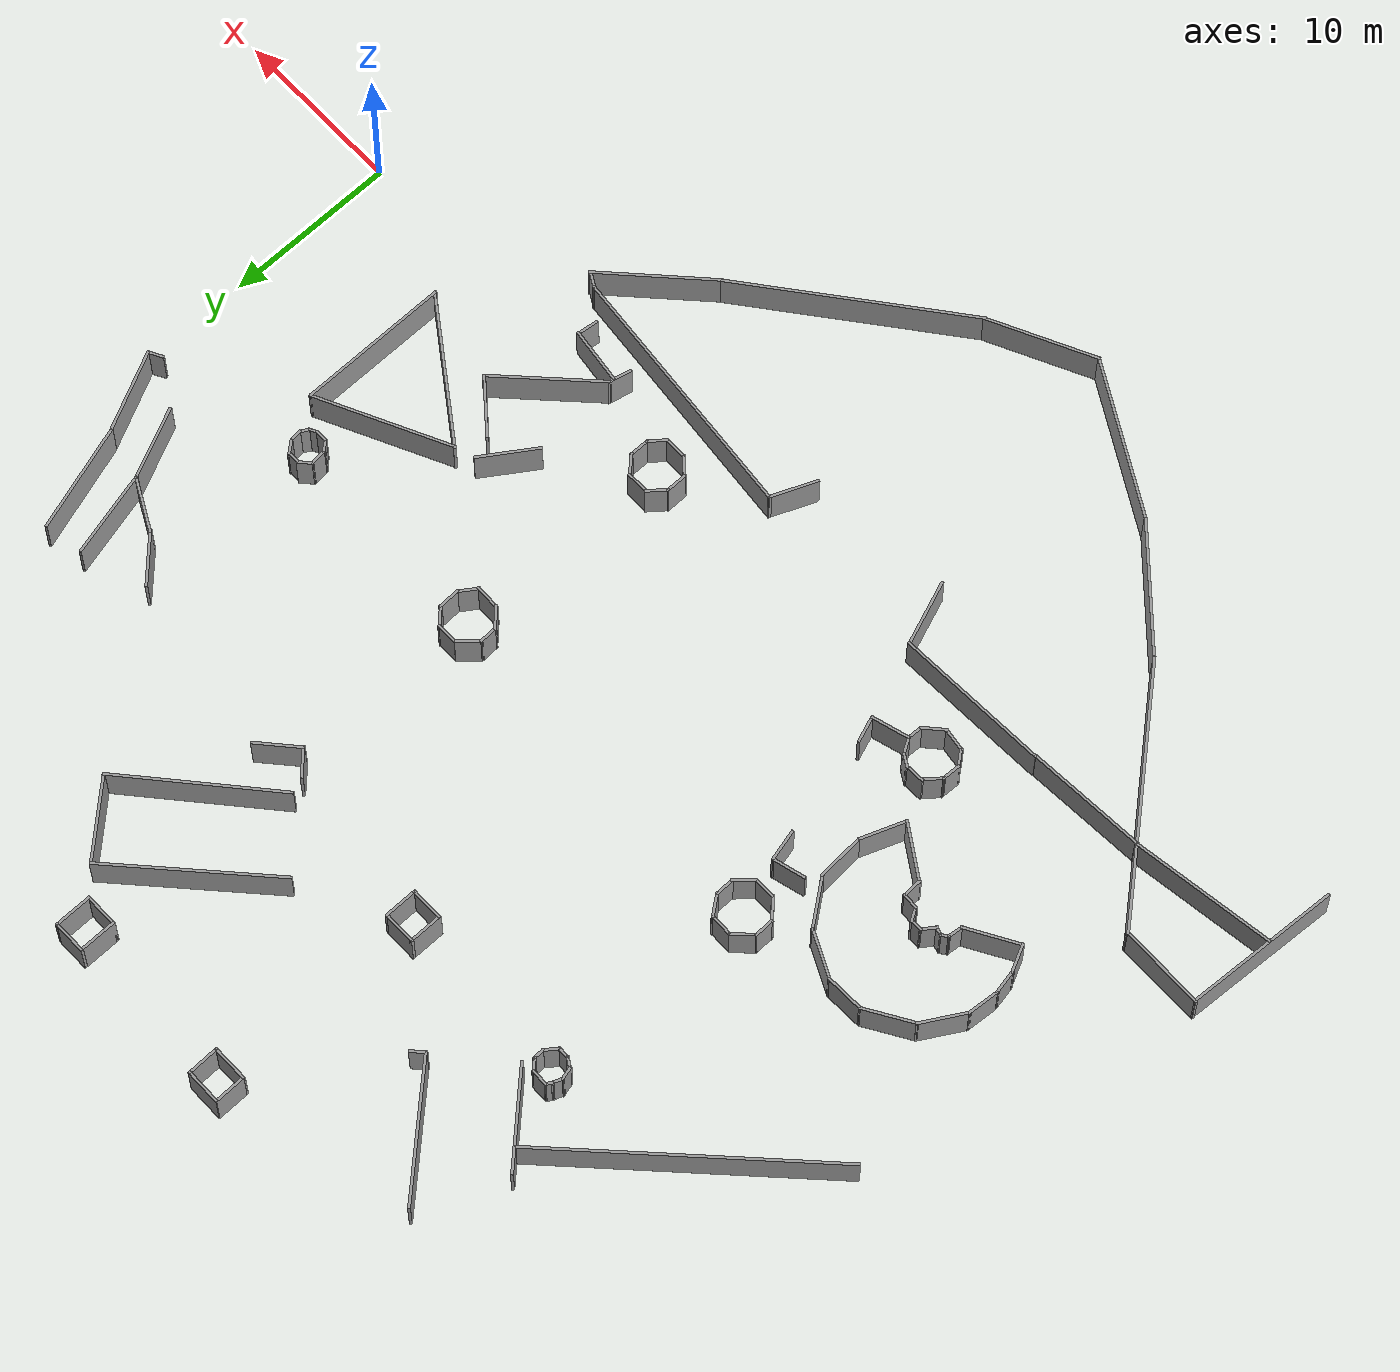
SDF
<?xml version='1.0'?>
<sdf version='1.6'>
  <model name='Area_B'>
    <pose frame=''>-32.1242 10.8214 0 0 -0 0</pose>
    <link name='Wall_121'>
      <collision name='Wall_121_Collision'>
        <geometry>
          <box>
            <size>3.88397 0.15 2.5</size>
          </box>
        </geometry>
        <pose frame=''>0 0 1.25 0 -0 0</pose>
      </collision>
      <visual name='Wall_121_Visual'>
        <pose frame=''>0 0 1.25 0 -0 0</pose>
        <geometry>
          <box>
            <size>3.88397 0.15 2.5</size>
          </box>
        </geometry>
        <material>
          <script>
            <uri>file://media/materials/scripts/gazebo.material</uri>
            <name>Gazebo/Grey</name>
          </script>
          <ambient>1 1 1 1</ambient>
        </material>
        <meta>
          <layer>0</layer>
        </meta>
      </visual>
      <pose frame=''>-6.68095 -13.663 0 0 -0 1.92212</pose>
    </link>
    <link name='Wall_122'>
      <collision name='Wall_122_Collision'>
        <geometry>
          <box>
            <size>8.9663 0.15 2.5</size>
          </box>
        </geometry>
        <pose frame=''>0 0 1.25 0 -0 0</pose>
      </collision>
      <visual name='Wall_122_Visual'>
        <pose frame=''>0 0 1.25 0 -0 0</pose>
        <geometry>
          <box>
            <size>8.9663 0.15 2.5</size>
          </box>
        </geometry>
        <material>
          <script>
            <uri>file://media/materials/scripts/gazebo.material</uri>
            <name>Gazebo/Grey</name>
          </script>
          <ambient>1 1 1 1</ambient>
        </material>
        <meta>
          <layer>0</layer>
        </meta>
      </visual>
      <pose frame=''>-11.7275 -12.0686 0 0 -0 -3.09867</pose>
    </link>
    <link name='Wall_123'>
      <collision name='Wall_123_Collision'>
        <geometry>
          <box>
            <size>7.06271 0.15 2.5</size>
          </box>
        </geometry>
        <pose frame=''>0 0 1.25 0 -0 0</pose>
      </collision>
      <visual name='Wall_123_Visual'>
        <pose frame=''>0 0 1.25 0 -0 0</pose>
        <geometry>
          <box>
            <size>7.06271 0.15 2.5</size>
          </box>
        </geometry>
        <material>
          <script>
            <uri>file://media/materials/scripts/gazebo.material</uri>
            <name>Gazebo/Grey</name>
          </script>
          <ambient>1 1 1 1</ambient>
        </material>
        <meta>
          <layer>0</layer>
        </meta>
      </visual>
      <pose frame=''>-19.5811 -12.5071 0 0 -0 -3.07824</pose>
    </link>
    <link name='Wall_124'>
      <collision name='Wall_124_Collision'>
        <geometry>
          <box>
            <size>10.3956 0.15 2.5</size>
          </box>
        </geometry>
        <pose frame=''>0 0 1.25 0 -0 0</pose>
      </collision>
      <visual name='Wall_124_Visual'>
        <pose frame=''>0 0 1.25 0 -0 0</pose>
        <geometry>
          <box>
            <size>10.3956 0.15 2.5</size>
          </box>
        </geometry>
        <material>
          <script>
            <uri>file://media/materials/scripts/gazebo.material</uri>
            <name>Gazebo/Grey</name>
          </script>
          <ambient>1 1 1 1</ambient>
        </material>
        <meta>
          <layer>0</layer>
        </meta>
      </visual>
      <pose frame=''>-19.7066 -16.5934 0 0 -0 -0.864734</pose>
    </link>
    <link name='Wall_125'>
      <collision name='Wall_125_Collision'>
        <geometry>
          <box>
            <size>7.87765 0.15 2.5</size>
          </box>
        </geometry>
        <pose frame=''>0 0 1.25 0 -0 0</pose>
      </collision>
      <visual name='Wall_125_Visual'>
        <pose frame=''>0 0 1.25 0 -0 0</pose>
        <geometry>
          <box>
            <size>7.87765 0.15 2.5</size>
          </box>
        </geometry>
        <material>
          <script>
            <uri>file://media/materials/scripts/gazebo.material</uri>
            <name>Gazebo/Grey</name>
          </script>
          <ambient>1 1 1 1</ambient>
        </material>
        <meta>
          <layer>0</layer>
        </meta>
      </visual>
      <pose frame=''>-13.4826 -23.0215 0 0 -0 -0.721859</pose>
    </link>
    <link name='Wall_126'>
      <collision name='Wall_126_Collision'>
        <geometry>
          <box>
            <size>9.61622 0.15 2.5</size>
          </box>
        </geometry>
        <pose frame=''>0 0 1.25 0 -0 0</pose>
      </collision>
      <visual name='Wall_126_Visual'>
        <pose frame=''>0 0 1.25 0 -0 0</pose>
        <geometry>
          <box>
            <size>9.61622 0.15 2.5</size>
          </box>
        </geometry>
        <material>
          <script>
            <uri>file://media/materials/scripts/gazebo.material</uri>
            <name>Gazebo/Grey</name>
          </script>
          <ambient>1 1 1 1</ambient>
        </material>
        <meta>
          <layer>0</layer>
        </meta>
      </visual>
      <pose frame=''>-6.48925 -27.9108 0 0 -0 -0.516207</pose>
    </link>
    <link name='Wall_127'>
      <collision name='Wall_127_Collision'>
        <geometry>
          <box>
            <size>6.48208 0.15 2.5</size>
          </box>
        </geometry>
        <pose frame=''>0 0 1.25 0 -0 0</pose>
      </collision>
      <visual name='Wall_127_Visual'>
        <pose frame=''>0 0 1.25 0 -0 0</pose>
        <geometry>
          <box>
            <size>6.48208 0.15 2.5</size>
          </box>
        </geometry>
        <material>
          <script>
            <uri>file://media/materials/scripts/gazebo.material</uri>
            <name>Gazebo/Grey</name>
          </script>
          <ambient>1 1 1 1</ambient>
        </material>
        <meta>
          <layer>0</layer>
        </meta>
      </visual>
      <pose frame=''>0.452913 -28.8669 0 0 -0 0.451121</pose>
    </link>
    <link name='Wall_128'>
      <collision name='Wall_128_Collision'>
        <geometry>
          <box>
            <size>14.028 0.15 2.5</size>
          </box>
        </geometry>
        <pose frame=''>0 0 1.25 0 -0 0</pose>
      </collision>
      <visual name='Wall_128_Visual'>
        <pose frame=''>0 0 1.25 0 -0 0</pose>
        <geometry>
          <box>
            <size>14.028 0.15 2.5</size>
          </box>
        </geometry>
        <material>
          <script>
            <uri>file://media/materials/scripts/gazebo.material</uri>
            <name>Gazebo/Grey</name>
          </script>
          <ambient>1 1 1 1</ambient>
        </material>
        <meta>
          <layer>0</layer>
        </meta>
      </visual>
      <pose frame=''>8.76594 -23.2328 0 0 -0 0.664139</pose>
    </link>
    <link name='Wall_129'>
      <collision name='Wall_129_Collision'>
        <geometry>
          <box>
            <size>7.08355 0.15 2.5</size>
          </box>
        </geometry>
        <pose frame=''>0 0 1.25 0 -0 0</pose>
      </collision>
      <visual name='Wall_129_Visual'>
        <pose frame=''>0 0 1.25 0 -0 0</pose>
        <geometry>
          <box>
            <size>7.08355 0.15 2.5</size>
          </box>
        </geometry>
        <material>
          <script>
            <uri>file://media/materials/scripts/gazebo.material</uri>
            <name>Gazebo/Grey</name>
          </script>
          <ambient>1 1 1 1</ambient>
        </material>
        <meta>
          <layer>0</layer>
        </meta>
      </visual>
      <pose frame=''>16.7843 -16.5789 0 0 -0 0.755438</pose>
    </link>
    <link name='Wall_130'>
      <collision name='Wall_130_Collision'>
        <geometry>
          <box>
            <size>1.1013 0.15 2.5</size>
          </box>
        </geometry>
        <pose frame=''>0 0 1.25 0 -0 0</pose>
      </collision>
      <visual name='Wall_130_Visual'>
        <pose frame=''>0 0 1.25 0 -0 0</pose>
        <geometry>
          <box>
            <size>1.1013 0.15 2.5</size>
          </box>
        </geometry>
        <material>
          <script>
            <uri>file://media/materials/scripts/gazebo.material</uri>
            <name>Gazebo/Grey</name>
          </script>
          <ambient>1 1 1 1</ambient>
        </material>
        <meta>
          <layer>0</layer>
        </meta>
      </visual>
      <pose frame=''>18.8914 -14.0032 0 0 -0 2.63826</pose>
    </link>
    <link name='Wall_131'>
      <collision name='Wall_131_Collision'>
        <geometry>
          <box>
            <size>15.2444 0.15 2.5</size>
          </box>
        </geometry>
        <pose frame=''>0 0 1.25 0 -0 0</pose>
      </collision>
      <visual name='Wall_131_Visual'>
        <pose frame=''>0 0 1.25 0 -0 0</pose>
        <geometry>
          <box>
            <size>15.2444 0.15 2.5</size>
          </box>
        </geometry>
        <material>
          <script>
            <uri>file://media/materials/scripts/gazebo.material</uri>
            <name>Gazebo/Grey</name>
          </script>
          <ambient>1 1 1 1</ambient>
        </material>
        <meta>
          <layer>0</layer>
        </meta>
      </visual>
      <pose frame=''>10.9971 -13.0073 0 0 -0 3.03986</pose>
    </link>
    <link name='Wall_132'>
      <collision name='Wall_132_Collision'>
        <geometry>
          <box>
            <size>2.83891 0.15 2.5</size>
          </box>
        </geometry>
        <pose frame=''>0 0 1.25 0 -0 0</pose>
      </collision>
      <visual name='Wall_132_Visual'>
        <pose frame=''>0 0 1.25 0 -0 0</pose>
        <geometry>
          <box>
            <size>2.83891 0.15 2.5</size>
          </box>
        </geometry>
        <material>
          <script>
            <uri>file://media/materials/scripts/gazebo.material</uri>
            <name>Gazebo/Grey</name>
          </script>
          <ambient>1 1 1 1</ambient>
        </material>
        <meta>
          <layer>0</layer>
        </meta>
      </visual>
      <pose frame=''>2.98945 -13.4764 0 0 -0 -1.97606</pose>
    </link>
    <link name='Wall_136'>
      <collision name='Wall_136_Collision'>
        <geometry>
          <box>
            <size>4.97543 0.15 2.5</size>
          </box>
        </geometry>
        <pose frame=''>0 0 1.25 0 -0 0</pose>
      </collision>
      <visual name='Wall_136_Visual'>
        <pose frame=''>0 0 1.25 0 -0 0</pose>
        <geometry>
          <box>
            <size>4.97543 0.15 2.5</size>
          </box>
        </geometry>
        <material>
          <script>
            <uri>file://media/materials/scripts/gazebo.material</uri>
            <name>Gazebo/Grey</name>
          </script>
          <ambient>1 1 1 1</ambient>
        </material>
        <meta>
          <layer>0</layer>
        </meta>
      </visual>
      <pose frame=''>-24.5908 -10.8551 0 0 -0 2.27406</pose>
    </link>
    <link name='Wall_137'>
      <collision name='Wall_137_Collision'>
        <geometry>
          <box>
            <size>5.04681 0.15 2.5</size>
          </box>
        </geometry>
        <pose frame=''>0 0 1.25 0 -0 0</pose>
      </collision>
      <visual name='Wall_137_Visual'>
        <pose frame=''>0 0 1.25 0 -0 0</pose>
        <geometry>
          <box>
            <size>5.04681 0.15 2.5</size>
          </box>
        </geometry>
        <material>
          <script>
            <uri>file://media/materials/scripts/gazebo.material</uri>
            <name>Gazebo/Grey</name>
          </script>
          <ambient>1 1 1 1</ambient>
        </material>
        <meta>
          <layer>0</layer>
        </meta>
      </visual>
      <pose frame=''>-28.5688 -8.98425 0 0 -0 3.1291</pose>
    </link>
    <link name='Wall_138'>
      <collision name='Wall_138_Collision'>
        <geometry>
          <box>
            <size>9.02765 0.15 2.5</size>
          </box>
        </geometry>
        <pose frame=''>0 0 1.25 0 -0 0</pose>
      </collision>
      <visual name='Wall_138_Visual'>
        <pose frame=''>0 0 1.25 0 -0 0</pose>
        <geometry>
          <box>
            <size>9.02765 0.15 2.5</size>
          </box>
        </geometry>
        <material>
          <script>
            <uri>file://media/materials/scripts/gazebo.material</uri>
            <name>Gazebo/Grey</name>
          </script>
          <ambient>1 1 1 1</ambient>
        </material>
        <meta>
          <layer>0</layer>
        </meta>
      </visual>
      <pose frame=''>-31.2617 -13.3839 0 0 -0 -1.63286</pose>
    </link>
    <link name='Wall_141'>
      <collision name='Wall_141_Collision'>
        <geometry>
          <box>
            <size>8.46011 0.15 2.5</size>
          </box>
        </geometry>
        <pose frame=''>0 0 1.25 0 -0 0</pose>
      </collision>
      <visual name='Wall_141_Visual'>
        <pose frame=''>0 0 1.25 0 -0 0</pose>
        <geometry>
          <box>
            <size>8.46011 0.15 2.5</size>
          </box>
        </geometry>
        <material>
          <script>
            <uri>file://media/materials/scripts/gazebo.material</uri>
            <name>Gazebo/Grey</name>
          </script>
          <ambient>1 1 1 1</ambient>
        </material>
        <meta>
          <layer>0</layer>
        </meta>
      </visual>
      <pose frame=''>-27.1416 -13.2978 0 0 -0 0.145493</pose>
    </link>
    <link name='Wall_144'>
      <collision name='Wall_144_Collision'>
        <geometry>
          <box>
            <size>3.57797 0.15 2.5</size>
          </box>
        </geometry>
        <pose frame=''>0 0 1.25 0 -0 0</pose>
      </collision>
      <visual name='Wall_144_Visual'>
        <pose frame=''>0 0 1.25 0 -0 0</pose>
        <geometry>
          <box>
            <size>3.57797 0.15 2.5</size>
          </box>
        </geometry>
        <material>
          <script>
            <uri>file://media/materials/scripts/gazebo.material</uri>
            <name>Gazebo/Grey</name>
          </script>
          <ambient>1 1 1 1</ambient>
        </material>
        <meta>
          <layer>0</layer>
        </meta>
      </visual>
      <pose frame=''>14.5292 -4.06296 0 0 -0 -2.1652</pose>
    </link>
    <link name='Wall_147'>
      <collision name='Wall_147_Collision'>
        <geometry>
          <box>
            <size>3.61382 0.15 2.5</size>
          </box>
        </geometry>
        <pose frame=''>0 0 1.25 0 -0 0</pose>
      </collision>
      <visual name='Wall_147_Visual'>
        <pose frame=''>0 0 1.25 0 -0 0</pose>
        <geometry>
          <box>
            <size>3.61382 0.15 2.5</size>
          </box>
        </geometry>
        <material>
          <script>
            <uri>file://media/materials/scripts/gazebo.material</uri>
            <name>Gazebo/Grey</name>
          </script>
          <ambient>1 1 1 1</ambient>
        </material>
        <meta>
          <layer>0</layer>
        </meta>
      </visual>
      <pose frame=''>17.2819 -5.0017 0 0 -0 -0.69159</pose>
    </link>
    <link name='Wall_148'>
      <collision name='Wall_148_Collision'>
        <geometry>
          <box>
            <size>6.69557 0.15 2.5</size>
          </box>
        </geometry>
        <pose frame=''>0 0 1.25 0 -0 0</pose>
      </collision>
      <visual name='Wall_148_Visual'>
        <pose frame=''>0 0 1.25 0 -0 0</pose>
        <geometry>
          <box>
            <size>6.69557 0.15 2.5</size>
          </box>
        </geometry>
        <material>
          <script>
            <uri>file://media/materials/scripts/gazebo.material</uri>
            <name>Gazebo/Grey</name>
          </script>
          <ambient>1 1 1 1</ambient>
        </material>
        <meta>
          <layer>0</layer>
        </meta>
      </visual>
      <pose frame=''>16.2943 -8.3819 0 0 -0 -2.37272</pose>
    </link>
    <link name='Wall_149'>
      <collision name='Wall_149_Collision'>
        <geometry>
          <box>
            <size>1.4258 0.15 2.5</size>
          </box>
        </geometry>
        <pose frame=''>0 0 1.25 0 -0 0</pose>
      </collision>
      <visual name='Wall_149_Visual'>
        <pose frame=''>0 0 1.25 0 -0 0</pose>
        <geometry>
          <box>
            <size>1.4258 0.15 2.5</size>
          </box>
        </geometry>
        <material>
          <script>
            <uri>file://media/materials/scripts/gazebo.material</uri>
            <name>Gazebo/Grey</name>
          </script>
          <ambient>1 1 1 1</ambient>
        </material>
        <meta>
          <layer>0</layer>
        </meta>
      </visual>
      <pose frame=''>13.7981 -11.2484 0 0 -0 -1.79868</pose>
    </link>
    <link name='Wall_154'>
      <collision name='Wall_154_Collision'>
        <geometry>
          <box>
            <size>3.35758 0.15 2.5</size>
          </box>
        </geometry>
        <pose frame=''>0 0 1.25 0 -0 0</pose>
      </collision>
      <visual name='Wall_154_Visual'>
        <pose frame=''>0 0 1.25 0 -0 0</pose>
        <geometry>
          <box>
            <size>3.35758 0.15 2.5</size>
          </box>
        </geometry>
        <material>
          <script>
            <uri>file://media/materials/scripts/gazebo.material</uri>
            <name>Gazebo/Grey</name>
          </script>
          <ambient>1 1 1 1</ambient>
        </material>
        <meta>
          <layer>0</layer>
        </meta>
      </visual>
      <pose frame=''>15.5179 -11.1505 0 0 -0 -0.136116</pose>
    </link>
    <link name='Wall_155'>
      <collision name='Wall_155_Collision'>
        <geometry>
          <box>
            <size>1.2865 0.15 2.5</size>
          </box>
        </geometry>
        <pose frame=''>0 0 1.25 0 -0 0</pose>
      </collision>
      <visual name='Wall_155_Visual'>
        <pose frame=''>0 0 1.25 0 -0 0</pose>
        <geometry>
          <box>
            <size>1.2865 0.15 2.5</size>
          </box>
        </geometry>
        <material>
          <script>
            <uri>file://media/materials/scripts/gazebo.material</uri>
            <name>Gazebo/Grey</name>
          </script>
          <ambient>1 1 1 1</ambient>
        </material>
        <meta>
          <layer>0</layer>
        </meta>
      </visual>
      <pose frame=''>17.0028 -11.9316 0 0 -0 -1.70058</pose>
    </link>
    <link name='Wall_158'>
      <collision name='Wall_158_Collision'>
        <geometry>
          <box>
            <size>8.1356 0.15 2.5</size>
          </box>
        </geometry>
        <pose frame=''>0 0 1.25 0 -0 0</pose>
      </collision>
      <visual name='Wall_158_Visual'>
        <pose frame=''>0 0 1.25 0 -0 0</pose>
        <geometry>
          <box>
            <size>8.1356 0.15 2.5</size>
          </box>
        </geometry>
        <material>
          <script>
            <uri>file://media/materials/scripts/gazebo.material</uri>
            <name>Gazebo/Grey</name>
          </script>
          <ambient>1 1 1 1</ambient>
        </material>
        <meta>
          <layer>0</layer>
        </meta>
      </visual>
      <pose frame=''>20.3182 -0.500974 0 0 -0 0.452021</pose>
    </link>
    <link name='Wall_159'>
      <collision name='Wall_159_Collision'>
        <geometry>
          <box>
            <size>8.83026 0.15 2.5</size>
          </box>
        </geometry>
        <pose frame=''>0 0 1.25 0 -0 0</pose>
      </collision>
      <visual name='Wall_159_Visual'>
        <pose frame=''>0 0 1.25 0 -0 0</pose>
        <geometry>
          <box>
            <size>8.83026 0.15 2.5</size>
          </box>
        </geometry>
        <material>
          <script>
            <uri>file://media/materials/scripts/gazebo.material</uri>
            <name>Gazebo/Grey</name>
          </script>
          <ambient>1 1 1 1</ambient>
        </material>
        <meta>
          <layer>0</layer>
        </meta>
      </visual>
      <pose frame=''>23.9185 -3.11471 0 0 -0 -1.56878</pose>
    </link>
    <link name='Wall_160'>
      <collision name='Wall_160_Collision'>
        <geometry>
          <box>
            <size>9.1362 0.15 2.5</size>
          </box>
        </geometry>
        <pose frame=''>0 0 1.25 0 -0 0</pose>
      </collision>
      <visual name='Wall_160_Visual'>
        <pose frame=''>0 0 1.25 0 -0 0</pose>
        <geometry>
          <box>
            <size>9.1362 0.15 2.5</size>
          </box>
        </geometry>
        <material>
          <script>
            <uri>file://media/materials/scripts/gazebo.material</uri>
            <name>Gazebo/Grey</name>
          </script>
          <ambient>1 1 1 1</ambient>
        </material>
        <meta>
          <layer>0</layer>
        </meta>
      </visual>
      <pose frame=''>20.2844 -4.84905 0 0 -0 2.52292</pose>
    </link>
    <link name='Wall_163'>
      <collision name='Wall_163_Collision'>
        <geometry>
          <box>
            <size>1.24033 0.15 2.5</size>
          </box>
        </geometry>
        <pose frame=''>0 0 1.25 0 -0 0</pose>
      </collision>
      <visual name='Wall_163_Visual'>
        <pose frame=''>0 0 1.25 0 -0 0</pose>
        <geometry>
          <box>
            <size>1.24033 0.15 2.5</size>
          </box>
        </geometry>
        <material>
          <script>
            <uri>file://media/materials/scripts/gazebo.material</uri>
            <name>Gazebo/Grey</name>
          </script>
          <ambient>1 1 1 1</ambient>
        </material>
        <meta>
          <layer>0</layer>
        </meta>
      </visual>
      <pose frame=''>-13.5147 -7.61319 0 0 -0 -2.26476</pose>
    </link>
    <link name='Wall_164'>
      <collision name='Wall_164_Collision'>
        <geometry>
          <box>
            <size>1.17243 0.15 2.5</size>
          </box>
        </geometry>
        <pose frame=''>0 0 1.25 0 -0 0</pose>
      </collision>
      <visual name='Wall_164_Visual'>
        <pose frame=''>0 0 1.25 0 -0 0</pose>
        <geometry>
          <box>
            <size>1.17243 0.15 2.5</size>
          </box>
        </geometry>
        <material>
          <script>
            <uri>file://media/materials/scripts/gazebo.material</uri>
            <name>Gazebo/Grey</name>
          </script>
          <ambient>1 1 1 1</ambient>
        </material>
        <meta>
          <layer>0</layer>
        </meta>
      </visual>
      <pose frame=''>-13.885 -8.5233 0 0 -0 -1.61316</pose>
    </link>
    <link name='Wall_165'>
      <collision name='Wall_165_Collision'>
        <geometry>
          <box>
            <size>1.05804 0.15 2.5</size>
          </box>
        </geometry>
        <pose frame=''>0 0 1.25 0 -0 0</pose>
      </collision>
      <visual name='Wall_165_Visual'>
        <pose frame=''>0 0 1.25 0 -0 0</pose>
        <geometry>
          <box>
            <size>1.05804 0.15 2.5</size>
          </box>
        </geometry>
        <material>
          <script>
            <uri>file://media/materials/scripts/gazebo.material</uri>
            <name>Gazebo/Grey</name>
          </script>
          <ambient>1 1 1 1</ambient>
        </material>
        <meta>
          <layer>0</layer>
        </meta>
      </visual>
      <pose frame=''>-13.6083 -9.39319 0 0 -0 -0.91103</pose>
    </link>
    <link name='Wall_166'>
      <collision name='Wall_166_Collision'>
        <geometry>
          <box>
            <size>1.427 0.15 2.5</size>
          </box>
        </geometry>
        <pose frame=''>0 0 1.25 0 -0 0</pose>
      </collision>
      <visual name='Wall_166_Visual'>
        <pose frame=''>0 0 1.25 0 -0 0</pose>
        <geometry>
          <box>
            <size>1.427 0.15 2.5</size>
          </box>
        </geometry>
        <material>
          <script>
            <uri>file://media/materials/scripts/gazebo.material</uri>
            <name>Gazebo/Grey</name>
          </script>
          <ambient>1 1 1 1</ambient>
        </material>
        <meta>
          <layer>0</layer>
        </meta>
      </visual>
      <pose frame=''>-12.6982 -9.8641 0 0 -0 -0.144696</pose>
    </link>
    <link name='Wall_167'>
      <collision name='Wall_167_Collision'>
        <geometry>
          <box>
            <size>1.45625 0.15 2.5</size>
          </box>
        </geometry>
        <pose frame=''>0 0 1.25 0 -0 0</pose>
      </collision>
      <visual name='Wall_167_Visual'>
        <pose frame=''>0 0 1.25 0 -0 0</pose>
        <geometry>
          <box>
            <size>1.45625 0.15 2.5</size>
          </box>
        </geometry>
        <material>
          <script>
            <uri>file://media/materials/scripts/gazebo.material</uri>
            <name>Gazebo/Grey</name>
          </script>
          <ambient>1 1 1 1</ambient>
        </material>
        <meta>
          <layer>0</layer>
        </meta>
      </visual>
      <pose frame=''>-11.58 -9.54037 0 0 -0 0.730738</pose>
    </link>
    <link name='Wall_168'>
      <collision name='Wall_168_Collision'>
        <geometry>
          <box>
            <size>0.972298 0.15 2.5</size>
          </box>
        </geometry>
        <pose frame=''>0 0 1.25 0 -0 0</pose>
      </collision>
      <visual name='Wall_168_Visual'>
        <pose frame=''>0 0 1.25 0 -0 0</pose>
        <geometry>
          <box>
            <size>0.972298 0.15 2.5</size>
          </box>
        </geometry>
        <material>
          <script>
            <uri>file://media/materials/scripts/gazebo.material</uri>
            <name>Gazebo/Grey</name>
          </script>
          <ambient>1 1 1 1</ambient>
        </material>
        <meta>
          <layer>0</layer>
        </meta>
      </visual>
      <pose frame=''>-11.0719 -8.67377 0 0 -0 1.51807</pose>
    </link>
    <link name='Wall_169'>
      <collision name='Wall_169_Collision'>
        <geometry>
          <box>
            <size>1.05324 0.15 2.5</size>
          </box>
        </geometry>
        <pose frame=''>0 0 1.25 0 -0 0</pose>
      </collision>
      <visual name='Wall_169_Visual'>
        <pose frame=''>0 0 1.25 0 -0 0</pose>
        <geometry>
          <box>
            <size>1.05324 0.15 2.5</size>
          </box>
        </geometry>
        <material>
          <script>
            <uri>file://media/materials/scripts/gazebo.material</uri>
            <name>Gazebo/Grey</name>
          </script>
          <ambient>1 1 1 1</ambient>
        </material>
        <meta>
          <layer>0</layer>
        </meta>
      </visual>
      <pose frame=''>-11.285 -7.87739 0 0 -0 2.11747</pose>
    </link>
    <link name='Wall_170'>
      <collision name='Wall_170_Collision'>
        <geometry>
          <box>
            <size>0.889481 0.15 2.5</size>
          </box>
        </geometry>
        <pose frame=''>0 0 1.25 0 -0 0</pose>
      </collision>
      <visual name='Wall_170_Visual'>
        <pose frame=''>0 0 1.25 0 -0 0</pose>
        <geometry>
          <box>
            <size>0.889481 0.15 2.5</size>
          </box>
        </geometry>
        <material>
          <script>
            <uri>file://media/materials/scripts/gazebo.material</uri>
            <name>Gazebo/Grey</name>
          </script>
          <ambient>1 1 1 1</ambient>
        </material>
        <meta>
          <layer>0</layer>
        </meta>
      </visual>
      <pose frame=''>-11.8383 -7.28371 0 0 -0 2.60891</pose>
    </link>
    <link name='Wall_171'>
      <collision name='Wall_171_Collision'>
        <geometry>
          <box>
            <size>1.17318 0.15 2.5</size>
          </box>
        </geometry>
        <pose frame=''>0 0 1.25 0 -0 0</pose>
      </collision>
      <visual name='Wall_171_Visual'>
        <pose frame=''>0 0 1.25 0 -0 0</pose>
        <geometry>
          <box>
            <size>1.17318 0.15 2.5</size>
          </box>
        </geometry>
        <material>
          <script>
            <uri>file://media/materials/scripts/gazebo.material</uri>
            <name>Gazebo/Grey</name>
          </script>
          <ambient>1 1 1 1</ambient>
        </material>
        <meta>
          <layer>0</layer>
        </meta>
      </visual>
      <pose frame=''>-12.668 -7.13616 0 0 -0 -3.10227</pose>
    </link>
    <link name='Wall_174'>
      <collision name='Wall_174_Collision'>
        <geometry>
          <box>
            <size>2.26077 0.15 2.5</size>
          </box>
        </geometry>
        <pose frame=''>0 0 1.25 0 -0 0</pose>
      </collision>
      <visual name='Wall_174_Visual'>
        <pose frame=''>0 0 1.25 0 -0 0</pose>
        <geometry>
          <box>
            <size>2.26077 0.15 2.5</size>
          </box>
        </geometry>
        <material>
          <script>
            <uri>file://media/materials/scripts/gazebo.material</uri>
            <name>Gazebo/Grey</name>
          </script>
          <ambient>1 1 1 1</ambient>
        </material>
        <meta>
          <layer>0</layer>
        </meta>
      </visual>
      <pose frame=''>-10.0159 -7.97132 0 0 -0 0.280209</pose>
    </link>
    <link name='Wall_175'>
      <collision name='Wall_175_Collision'>
        <geometry>
          <box>
            <size>1.61868 0.15 2.5</size>
          </box>
        </geometry>
        <pose frame=''>0 0 1.25 0 -0 0</pose>
      </collision>
      <visual name='Wall_175_Visual'>
        <pose frame=''>0 0 1.25 0 -0 0</pose>
        <geometry>
          <box>
            <size>1.61868 0.15 2.5</size>
          </box>
        </geometry>
        <material>
          <script>
            <uri>file://media/materials/scripts/gazebo.material</uri>
            <name>Gazebo/Grey</name>
          </script>
          <ambient>1 1 1 1</ambient>
        </material>
        <meta>
          <layer>0</layer>
        </meta>
      </visual>
      <pose frame=''>-9.2267 -6.98722 0 0 -0 1.9111</pose>
    </link>
    <link name='Wall_178'>
      <collision name='Wall_178_Collision'>
        <geometry>
          <box>
            <size>2 0.15 2.5</size>
          </box>
        </geometry>
        <pose frame=''>0 0 1.25 0 -0 0</pose>
      </collision>
      <visual name='Wall_178_Visual'>
        <pose frame=''>0 0 1.25 0 -0 0</pose>
        <geometry>
          <box>
            <size>2 0.15 2.5</size>
          </box>
        </geometry>
        <material>
          <script>
            <uri>file://media/materials/scripts/gazebo.material</uri>
            <name>Gazebo/Grey</name>
          </script>
          <ambient>1 1 1 1</ambient>
        </material>
        <meta>
          <layer>0</layer>
        </meta>
      </visual>
      <pose frame=''>-12.0714 1.0505 0 0 -0 0.261799</pose>
    </link>
    <link name='Wall_179'>
      <collision name='Wall_179_Collision'>
        <geometry>
          <box>
            <size>1.90592 0.15 2.5</size>
          </box>
        </geometry>
        <pose frame=''>0 0 1.25 0 -0 0</pose>
      </collision>
      <visual name='Wall_179_Visual'>
        <pose frame=''>0 0 1.25 0 -0 0</pose>
        <geometry>
          <box>
            <size>1.90592 0.15 2.5</size>
          </box>
        </geometry>
        <material>
          <script>
            <uri>file://media/materials/scripts/gazebo.material</uri>
            <name>Gazebo/Grey</name>
          </script>
          <ambient>1 1 1 1</ambient>
        </material>
        <meta>
          <layer>0</layer>
        </meta>
      </visual>
      <pose frame=''>-10.9708 0.436711 0 0 -0 -1.33272</pose>
    </link>
    <link name='Wall_182'>
      <collision name='Wall_182_Collision'>
        <geometry>
          <box>
            <size>1.35124 0.15 2.5</size>
          </box>
        </geometry>
        <pose frame=''>0 0 1.25 0 -0 0</pose>
      </collision>
      <visual name='Wall_182_Visual'>
        <pose frame=''>0 0 1.25 0 -0 0</pose>
        <geometry>
          <box>
            <size>1.35124 0.15 2.5</size>
          </box>
        </geometry>
        <material>
          <script>
            <uri>file://media/materials/scripts/gazebo.material</uri>
            <name>Gazebo/Grey</name>
          </script>
          <ambient>1 1 1 1</ambient>
        </material>
        <meta>
          <layer>0</layer>
        </meta>
      </visual>
      <pose frame=''>-11.9623 5.61824 0 0 -0 -0.033494</pose>
    </link>
    <link name='Wall_183'>
      <collision name='Wall_183_Collision'>
        <geometry>
          <box>
            <size>1.42592 0.15 2.5</size>
          </box>
        </geometry>
        <pose frame=''>0 0 1.25 0 -0 0</pose>
      </collision>
      <visual name='Wall_183_Visual'>
        <pose frame=''>0 0 1.25 0 -0 0</pose>
        <geometry>
          <box>
            <size>1.42592 0.15 2.5</size>
          </box>
        </geometry>
        <material>
          <script>
            <uri>file://media/materials/scripts/gazebo.material</uri>
            <name>Gazebo/Grey</name>
          </script>
          <ambient>1 1 1 1</ambient>
        </material>
        <meta>
          <layer>0</layer>
        </meta>
      </visual>
      <pose frame=''>-10.981 5.10652 0 0 -0 -0.930819</pose>
    </link>
    <link name='Wall_184'>
      <collision name='Wall_184_Collision'>
        <geometry>
          <box>
            <size>1.15807 0.15 2.5</size>
          </box>
        </geometry>
        <pose frame=''>0 0 1.25 0 -0 0</pose>
      </collision>
      <visual name='Wall_184_Visual'>
        <pose frame=''>0 0 1.25 0 -0 0</pose>
        <geometry>
          <box>
            <size>1.15807 0.15 2.5</size>
          </box>
        </geometry>
        <material>
          <script>
            <uri>file://media/materials/scripts/gazebo.material</uri>
            <name>Gazebo/Grey</name>
          </script>
          <ambient>1 1 1 1</ambient>
        </material>
        <meta>
          <layer>0</layer>
        </meta>
      </visual>
      <pose frame=''>-10.6202 4.09077 0 0 -0 -1.5708</pose>
    </link>
    <link name='Wall_185'>
      <collision name='Wall_185_Collision'>
        <geometry>
          <box>
            <size>1.37174 0.15 2.5</size>
          </box>
        </geometry>
        <pose frame=''>0 0 1.25 0 -0 0</pose>
      </collision>
      <visual name='Wall_185_Visual'>
        <pose frame=''>0 0 1.25 0 -0 0</pose>
        <geometry>
          <box>
            <size>1.37174 0.15 2.5</size>
          </box>
        </geometry>
        <material>
          <script>
            <uri>file://media/materials/scripts/gazebo.material</uri>
            <name>Gazebo/Grey</name>
          </script>
          <ambient>1 1 1 1</ambient>
        </material>
        <meta>
          <layer>0</layer>
        </meta>
      </visual>
      <pose frame=''>-11.0036 3.12817 0 0 -0 -2.2925</pose>
    </link>
    <link name='Wall_186'>
      <collision name='Wall_186_Collision'>
        <geometry>
          <box>
            <size>1.31898 0.15 2.5</size>
          </box>
        </geometry>
        <pose frame=''>0 0 1.25 0 -0 0</pose>
      </collision>
      <visual name='Wall_186_Visual'>
        <pose frame=''>0 0 1.25 0 -0 0</pose>
        <geometry>
          <box>
            <size>1.31898 0.15 2.5</size>
          </box>
        </geometry>
        <material>
          <script>
            <uri>file://media/materials/scripts/gazebo.material</uri>
            <name>Gazebo/Grey</name>
          </script>
          <ambient>1 1 1 1</ambient>
        </material>
        <meta>
          <layer>0</layer>
        </meta>
      </visual>
      <pose frame=''>-12.0118 2.6696 0 0 -0 3.14159</pose>
    </link>
    <link name='Wall_187'>
      <collision name='Wall_187_Collision'>
        <geometry>
          <box>
            <size>1.49728 0.15 2.5</size>
          </box>
        </geometry>
        <pose frame=''>0 0 1.25 0 -0 0</pose>
      </collision>
      <visual name='Wall_187_Visual'>
        <pose frame=''>0 0 1.25 0 -0 0</pose>
        <geometry>
          <box>
            <size>1.49728 0.15 2.5</size>
          </box>
        </geometry>
        <material>
          <script>
            <uri>file://media/materials/scripts/gazebo.material</uri>
            <name>Gazebo/Grey</name>
          </script>
          <ambient>1 1 1 1</ambient>
        </material>
        <meta>
          <layer>0</layer>
        </meta>
      </visual>
      <pose frame=''>-13.0951 3.14357 0 0 -0 2.36114</pose>
    </link>
    <link name='Wall_188'>
      <collision name='Wall_188_Collision'>
        <geometry>
          <box>
            <size>1.21321 0.15 2.5</size>
          </box>
        </geometry>
        <pose frame=''>0 0 1.25 0 -0 0</pose>
      </collision>
      <visual name='Wall_188_Visual'>
        <pose frame=''>0 0 1.25 0 -0 0</pose>
        <geometry>
          <box>
            <size>1.21321 0.15 2.5</size>
          </box>
        </geometry>
        <material>
          <script>
            <uri>file://media/materials/scripts/gazebo.material</uri>
            <name>Gazebo/Grey</name>
          </script>
          <ambient>1 1 1 1</ambient>
        </material>
        <meta>
          <layer>0</layer>
        </meta>
      </visual>
      <pose frame=''>-13.5631 4.14875 0 0 -0 1.58855</pose>
    </link>
    <link name='Wall_189'>
      <collision name='Wall_189_Collision'>
        <geometry>
          <box>
            <size>1.46883 0.15 2.5</size>
          </box>
        </geometry>
        <pose frame=''>0 0 1.25 0 -0 0</pose>
      </collision>
      <visual name='Wall_189_Visual'>
        <pose frame=''>0 0 1.25 0 -0 0</pose>
        <geometry>
          <box>
            <size>1.46883 0.15 2.5</size>
          </box>
        </geometry>
        <material>
          <script>
            <uri>file://media/materials/scripts/gazebo.material</uri>
            <name>Gazebo/Grey</name>
          </script>
          <ambient>1 1 1 1</ambient>
        </material>
        <meta>
          <layer>0</layer>
        </meta>
      </visual>
      <pose frame=''>-13.0964 5.15626 0 0 -0 0.807159</pose>
    </link>
    <link name='Wall_192'>
      <collision name='Wall_192_Collision'>
        <geometry>
          <box>
            <size>1.33063 0.15 2.5</size>
          </box>
        </geometry>
        <pose frame=''>0 0 1.25 0 -0 0</pose>
      </collision>
      <visual name='Wall_192_Visual'>
        <pose frame=''>0 0 1.25 0 -0 0</pose>
        <geometry>
          <box>
            <size>1.33063 0.15 2.5</size>
          </box>
        </geometry>
        <material>
          <script>
            <uri>file://media/materials/scripts/gazebo.material</uri>
            <name>Gazebo/Grey</name>
          </script>
          <ambient>1 1 1 1</ambient>
        </material>
        <meta>
          <layer>0</layer>
        </meta>
      </visual>
      <pose frame=''>8.74463 -7.81763 0 0 -0 0</pose>
    </link>
    <link name='Wall_193'>
      <collision name='Wall_193_Collision'>
        <geometry>
          <box>
            <size>1.31589 0.15 2.5</size>
          </box>
        </geometry>
        <pose frame=''>0 0 1.25 0 -0 0</pose>
      </collision>
      <visual name='Wall_193_Visual'>
        <pose frame=''>0 0 1.25 0 -0 0</pose>
        <geometry>
          <box>
            <size>1.31589 0.15 2.5</size>
          </box>
        </geometry>
        <material>
          <script>
            <uri>file://media/materials/scripts/gazebo.material</uri>
            <name>Gazebo/Grey</name>
          </script>
          <ambient>1 1 1 1</ambient>
        </material>
        <meta>
          <layer>0</layer>
        </meta>
      </visual>
      <pose frame=''>9.7317 -8.26476 0 0 -0 -0.822003</pose>
    </link>
    <link name='Wall_194'>
      <collision name='Wall_194_Collision'>
        <geometry>
          <box>
            <size>1.20977 0.15 2.5</size>
          </box>
        </geometry>
        <pose frame=''>0 0 1.25 0 -0 0</pose>
      </collision>
      <visual name='Wall_194_Visual'>
        <pose frame=''>0 0 1.25 0 -0 0</pose>
        <geometry>
          <box>
            <size>1.20977 0.15 2.5</size>
          </box>
        </geometry>
        <material>
          <script>
            <uri>file://media/materials/scripts/gazebo.material</uri>
            <name>Gazebo/Grey</name>
          </script>
          <ambient>1 1 1 1</ambient>
        </material>
        <meta>
          <layer>0</layer>
        </meta>
      </visual>
      <pose frame=''>10.1084 -9.22166 0 0 -0 -1.5708</pose>
    </link>
    <link name='Wall_195'>
      <collision name='Wall_195_Collision'>
        <geometry>
          <box>
            <size>1.1993 0.15 2.5</size>
          </box>
        </geometry>
        <pose frame=''>0 0 1.25 0 -0 0</pose>
      </collision>
      <visual name='Wall_195_Visual'>
        <pose frame=''>0 0 1.25 0 -0 0</pose>
        <geometry>
          <box>
            <size>1.1993 0.15 2.5</size>
          </box>
        </geometry>
        <material>
          <script>
            <uri>file://media/materials/scripts/gazebo.material</uri>
            <name>Gazebo/Grey</name>
          </script>
          <ambient>1 1 1 1</ambient>
        </material>
        <meta>
          <layer>0</layer>
        </meta>
      </visual>
      <pose frame=''>9.77986 -10.1807 0 0 -0 -2.24755</pose>
    </link>
    <link name='Wall_196'>
      <collision name='Wall_196_Collision'>
        <geometry>
          <box>
            <size>1.3908 0.15 2.5</size>
          </box>
        </geometry>
        <pose frame=''>0 0 1.25 0 -0 0</pose>
      </collision>
      <visual name='Wall_196_Visual'>
        <pose frame=''>0 0 1.25 0 -0 0</pose>
        <geometry>
          <box>
            <size>1.3908 0.15 2.5</size>
          </box>
        </geometry>
        <material>
          <script>
            <uri>file://media/materials/scripts/gazebo.material</uri>
            <name>Gazebo/Grey</name>
          </script>
          <ambient>1 1 1 1</ambient>
        </material>
        <meta>
          <layer>0</layer>
        </meta>
      </visual>
      <pose frame=''>8.85101 -10.5897 0 0 -0 3.14159</pose>
    </link>
    <link name='Wall_197'>
      <collision name='Wall_197_Collision'>
        <geometry>
          <box>
            <size>1.32941 0.15 2.5</size>
          </box>
        </geometry>
        <pose frame=''>0 0 1.25 0 -0 0</pose>
      </collision>
      <visual name='Wall_197_Visual'>
        <pose frame=''>0 0 1.25 0 -0 0</pose>
        <geometry>
          <box>
            <size>1.32941 0.15 2.5</size>
          </box>
        </geometry>
        <material>
          <script>
            <uri>file://media/materials/scripts/gazebo.material</uri>
            <name>Gazebo/Grey</name>
          </script>
          <ambient>1 1 1 1</ambient>
        </material>
        <meta>
          <layer>0</layer>
        </meta>
      </visual>
      <pose frame=''>7.78447 -10.2242 0 0 -0 2.42883</pose>
    </link>
    <link name='Wall_198'>
      <collision name='Wall_198_Collision'>
        <geometry>
          <box>
            <size>1.31034 0.15 2.5</size>
          </box>
        </geometry>
        <pose frame=''>0 0 1.25 0 -0 0</pose>
      </collision>
      <visual name='Wall_198_Visual'>
        <pose frame=''>0 0 1.25 0 -0 0</pose>
        <geometry>
          <box>
            <size>1.31034 0.15 2.5</size>
          </box>
        </geometry>
        <material>
          <script>
            <uri>file://media/materials/scripts/gazebo.material</uri>
            <name>Gazebo/Grey</name>
          </script>
          <ambient>1 1 1 1</ambient>
        </material>
        <meta>
          <layer>0</layer>
        </meta>
      </visual>
      <pose frame=''>7.33832 -9.27851 0 0 -0 1.5708</pose>
    </link>
    <link name='Wall_199'>
      <collision name='Wall_199_Collision'>
        <geometry>
          <box>
            <size>1.28988 0.15 2.5</size>
          </box>
        </geometry>
        <pose frame=''>0 0 1.25 0 -0 0</pose>
      </collision>
      <visual name='Wall_199_Visual'>
        <pose frame=''>0 0 1.25 0 -0 0</pose>
        <geometry>
          <box>
            <size>1.28988 0.15 2.5</size>
          </box>
        </geometry>
        <material>
          <script>
            <uri>file://media/materials/scripts/gazebo.material</uri>
            <name>Gazebo/Grey</name>
          </script>
          <ambient>1 1 1 1</ambient>
        </material>
        <meta>
          <layer>0</layer>
        </meta>
      </visual>
      <pose frame=''>7.71986 -8.25765 0 0 -0 0.883907</pose>
    </link>
    <link name='Wall_202'>
      <collision name='Wall_202_Collision'>
        <geometry>
          <box>
            <size>1.25 0.15 2.5</size>
          </box>
        </geometry>
        <pose frame=''>0 0 1.25 0 -0 0</pose>
      </collision>
      <visual name='Wall_202_Visual'>
        <pose frame=''>0 0 1.25 0 -0 0</pose>
        <geometry>
          <box>
            <size>1.25 0.15 2.5</size>
          </box>
        </geometry>
        <material>
          <script>
            <uri>file://media/materials/scripts/gazebo.material</uri>
            <name>Gazebo/Grey</name>
          </script>
          <ambient>1 1 1 1</ambient>
        </material>
        <meta>
          <layer>0</layer>
        </meta>
      </visual>
      <pose frame=''>9.1469 5.05506 0 0 -0 0</pose>
    </link>
    <link name='Wall_203'>
      <collision name='Wall_203_Collision'>
        <geometry>
          <box>
            <size>1.25 0.15 2.5</size>
          </box>
        </geometry>
        <pose frame=''>0 0 1.25 0 -0 0</pose>
      </collision>
      <visual name='Wall_203_Visual'>
        <pose frame=''>0 0 1.25 0 -0 0</pose>
        <geometry>
          <box>
            <size>1.25 0.15 2.5</size>
          </box>
        </geometry>
        <material>
          <script>
            <uri>file://media/materials/scripts/gazebo.material</uri>
            <name>Gazebo/Grey</name>
          </script>
          <ambient>1 1 1 1</ambient>
        </material>
        <meta>
          <layer>0</layer>
        </meta>
      </visual>
      <pose frame=''>10.0858 4.66615 0 0 -0 -0.785398</pose>
    </link>
    <link name='Wall_204'>
      <collision name='Wall_204_Collision'>
        <geometry>
          <box>
            <size>1.35124 0.15 2.5</size>
          </box>
        </geometry>
        <pose frame=''>0 0 1.25 0 -0 0</pose>
      </collision>
      <visual name='Wall_204_Visual'>
        <pose frame=''>0 0 1.25 0 -0 0</pose>
        <geometry>
          <box>
            <size>1.35124 0.15 2.5</size>
          </box>
        </geometry>
        <material>
          <script>
            <uri>file://media/materials/scripts/gazebo.material</uri>
            <name>Gazebo/Grey</name>
          </script>
          <ambient>1 1 1 1</ambient>
        </material>
        <meta>
          <layer>0</layer>
        </meta>
      </visual>
      <pose frame=''>10.4948 3.67695 0 0 -0 -1.5373</pose>
    </link>
    <link name='Wall_205'>
      <collision name='Wall_205_Collision'>
        <geometry>
          <box>
            <size>1.23106 0.15 2.5</size>
          </box>
        </geometry>
        <pose frame=''>0 0 1.25 0 -0 0</pose>
      </collision>
      <visual name='Wall_205_Visual'>
        <pose frame=''>0 0 1.25 0 -0 0</pose>
        <geometry>
          <box>
            <size>1.23106 0.15 2.5</size>
          </box>
        </geometry>
        <material>
          <script>
            <uri>file://media/materials/scripts/gazebo.material</uri>
            <name>Gazebo/Grey</name>
          </script>
          <ambient>1 1 1 1</ambient>
        </material>
        <meta>
          <layer>0</layer>
        </meta>
      </visual>
      <pose frame=''>10.1897 2.63053 0 0 -0 -2.17072</pose>
    </link>
    <link name='Wall_206'>
      <collision name='Wall_206_Collision'>
        <geometry>
          <box>
            <size>1.50015 0.15 2.5</size>
          </box>
        </geometry>
        <pose frame=''>0 0 1.25 0 -0 0</pose>
      </collision>
      <visual name='Wall_206_Visual'>
        <pose frame=''>0 0 1.25 0 -0 0</pose>
        <geometry>
          <box>
            <size>1.50015 0.15 2.5</size>
          </box>
        </geometry>
        <material>
          <script>
            <uri>file://media/materials/scripts/gazebo.material</uri>
            <name>Gazebo/Grey</name>
          </script>
          <ambient>1 1 1 1</ambient>
        </material>
        <meta>
          <layer>0</layer>
        </meta>
      </visual>
      <pose frame=''>9.2296 2.19444 0 0 -0 3.12669</pose>
    </link>
    <link name='Wall_207'>
      <collision name='Wall_207_Collision'>
        <geometry>
          <box>
            <size>1.41467 0.15 2.5</size>
          </box>
        </geometry>
        <pose frame=''>0 0 1.25 0 -0 0</pose>
      </collision>
      <visual name='Wall_207_Visual'>
        <pose frame=''>0 0 1.25 0 -0 0</pose>
        <geometry>
          <box>
            <size>1.41467 0.15 2.5</size>
          </box>
        </geometry>
        <material>
          <script>
            <uri>file://media/materials/scripts/gazebo.material</uri>
            <name>Gazebo/Grey</name>
          </script>
          <ambient>1 1 1 1</ambient>
        </material>
        <meta>
          <layer>0</layer>
        </meta>
      </visual>
      <pose frame=''>8.10748 2.63151 0 0 -0 2.35619</pose>
    </link>
    <link name='Wall_208'>
      <collision name='Wall_208_Collision'>
        <geometry>
          <box>
            <size>1.08995 0.15 2.5</size>
          </box>
        </geometry>
        <pose frame=''>0 0 1.25 0 -0 0</pose>
      </collision>
      <visual name='Wall_208_Visual'>
        <pose frame=''>0 0 1.25 0 -0 0</pose>
        <geometry>
          <box>
            <size>1.08995 0.15 2.5</size>
          </box>
        </geometry>
        <material>
          <script>
            <uri>file://media/materials/scripts/gazebo.material</uri>
            <name>Gazebo/Grey</name>
          </script>
          <ambient>1 1 1 1</ambient>
        </material>
        <meta>
          <layer>0</layer>
        </meta>
      </visual>
      <pose frame=''>7.64024 3.56829 0 0 -0 1.61361</pose>
    </link>
    <link name='Wall_209'>
      <collision name='Wall_209_Collision'>
        <geometry>
          <box>
            <size>1.45791 0.15 2.5</size>
          </box>
        </geometry>
        <pose frame=''>0 0 1.25 0 -0 0</pose>
      </collision>
      <visual name='Wall_209_Visual'>
        <pose frame=''>0 0 1.25 0 -0 0</pose>
        <geometry>
          <box>
            <size>1.45791 0.15 2.5</size>
          </box>
        </geometry>
        <material>
          <script>
            <uri>file://media/materials/scripts/gazebo.material</uri>
            <name>Gazebo/Grey</name>
          </script>
          <ambient>1 1 1 1</ambient>
        </material>
        <meta>
          <layer>0</layer>
        </meta>
      </visual>
      <pose frame=''>8.0715 4.52944 0 0 -0 0.85069</pose>
    </link>
    <link name='Wall_212'>
      <collision name='Wall_212_Collision'>
        <geometry>
          <box>
            <size>2 0.15 2.5</size>
          </box>
        </geometry>
        <pose frame=''>0 0 1.25 0 -0 0</pose>
      </collision>
      <visual name='Wall_212_Visual'>
        <pose frame=''>0 0 1.25 0 -0 0</pose>
        <geometry>
          <box>
            <size>2 0.15 2.5</size>
          </box>
        </geometry>
        <material>
          <script>
            <uri>file://media/materials/scripts/gazebo.material</uri>
            <name>Gazebo/Grey</name>
          </script>
          <ambient>1 1 1 1</ambient>
        </material>
        <meta>
          <layer>0</layer>
        </meta>
      </visual>
      <pose frame=''>-2.05802 16.6093 0 0 -0 -1.5708</pose>
    </link>
    <link name='Wall_213'>
      <collision name='Wall_213_Collision'>
        <geometry>
          <box>
            <size>2 0.15 2.5</size>
          </box>
        </geometry>
        <pose frame=''>0 0 1.25 0 -0 0</pose>
      </collision>
      <visual name='Wall_213_Visual'>
        <pose frame=''>0 0 1.25 0 -0 0</pose>
        <geometry>
          <box>
            <size>2 0.15 2.5</size>
          </box>
        </geometry>
        <material>
          <script>
            <uri>file://media/materials/scripts/gazebo.material</uri>
            <name>Gazebo/Grey</name>
          </script>
          <ambient>1 1 1 1</ambient>
        </material>
        <meta>
          <layer>0</layer>
        </meta>
      </visual>
      <pose frame=''>-1.13302 15.6843 0 0 -0 0</pose>
    </link>
    <link name='Wall_214'>
      <collision name='Wall_214_Collision'>
        <geometry>
          <box>
            <size>2 0.15 2.5</size>
          </box>
        </geometry>
        <pose frame=''>0 0 1.25 0 -0 0</pose>
      </collision>
      <visual name='Wall_214_Visual'>
        <pose frame=''>0 0 1.25 0 -0 0</pose>
        <geometry>
          <box>
            <size>2 0.15 2.5</size>
          </box>
        </geometry>
        <material>
          <script>
            <uri>file://media/materials/scripts/gazebo.material</uri>
            <name>Gazebo/Grey</name>
          </script>
          <ambient>1 1 1 1</ambient>
        </material>
        <meta>
          <layer>0</layer>
        </meta>
      </visual>
      <pose frame=''>-0.208026 16.6093 0 0 -0 1.5708</pose>
    </link>
    <link name='Wall_215'>
      <collision name='Wall_215_Collision'>
        <geometry>
          <box>
            <size>2 0.15 2.5</size>
          </box>
        </geometry>
        <pose frame=''>0 0 1.25 0 -0 0</pose>
      </collision>
      <visual name='Wall_215_Visual'>
        <pose frame=''>0 0 1.25 0 -0 0</pose>
        <geometry>
          <box>
            <size>2 0.15 2.5</size>
          </box>
        </geometry>
        <material>
          <script>
            <uri>file://media/materials/scripts/gazebo.material</uri>
            <name>Gazebo/Grey</name>
          </script>
          <ambient>1 1 1 1</ambient>
        </material>
        <meta>
          <layer>0</layer>
        </meta>
      </visual>
      <pose frame=''>-1.13302 17.5343 0 0 -0 3.14159</pose>
    </link>
    <link name='Wall_218'>
      <collision name='Wall_218_Collision'>
        <geometry>
          <box>
            <size>1.89001 0.15 2.5</size>
          </box>
        </geometry>
        <pose frame=''>0 0 1.25 0 -0 0</pose>
      </collision>
      <visual name='Wall_218_Visual'>
        <pose frame=''>0 0 1.25 0 -0 0</pose>
        <geometry>
          <box>
            <size>1.89001 0.15 2.5</size>
          </box>
        </geometry>
        <material>
          <script>
            <uri>file://media/materials/scripts/gazebo.material</uri>
            <name>Gazebo/Grey</name>
          </script>
          <ambient>1 1 1 1</ambient>
        </material>
        <meta>
          <layer>0</layer>
        </meta>
      </visual>
      <pose frame=''>-1.76944 29.3796 0 0 -0 -1.56074</pose>
    </link>
    <link name='Wall_219'>
      <collision name='Wall_219_Collision'>
        <geometry>
          <box>
            <size>2.16255 0.15 2.5</size>
          </box>
        </geometry>
        <pose frame=''>0 0 1.25 0 -0 0</pose>
      </collision>
      <visual name='Wall_219_Visual'>
        <pose frame=''>0 0 1.25 0 -0 0</pose>
        <geometry>
          <box>
            <size>2.16255 0.15 2.5</size>
          </box>
        </geometry>
        <material>
          <script>
            <uri>file://media/materials/scripts/gazebo.material</uri>
            <name>Gazebo/Grey</name>
          </script>
          <ambient>1 1 1 1</ambient>
        </material>
        <meta>
          <layer>0</layer>
        </meta>
      </visual>
      <pose frame=''>-0.75442 28.4922 0 0 -0 0</pose>
    </link>
    <link name='Wall_220'>
      <collision name='Wall_220_Collision'>
        <geometry>
          <box>
            <size>1.90262 0.15 2.5</size>
          </box>
        </geometry>
        <pose frame=''>0 0 1.25 0 -0 0</pose>
      </collision>
      <visual name='Wall_220_Visual'>
        <pose frame=''>0 0 1.25 0 -0 0</pose>
        <geometry>
          <box>
            <size>1.90262 0.15 2.5</size>
          </box>
        </geometry>
        <material>
          <script>
            <uri>file://media/materials/scripts/gazebo.material</uri>
            <name>Gazebo/Grey</name>
          </script>
          <ambient>1 1 1 1</ambient>
        </material>
        <meta>
          <layer>0</layer>
        </meta>
      </visual>
      <pose frame=''>0.251855 29.3683 0 0 -0 1.59076</pose>
    </link>
    <link name='Wall_221'>
      <collision name='Wall_221_Collision'>
        <geometry>
          <box>
            <size>2.13277 0.15 2.5</size>
          </box>
        </geometry>
        <pose frame=''>0 0 1.25 0 -0 0</pose>
      </collision>
      <visual name='Wall_221_Visual'>
        <pose frame=''>0 0 1.25 0 -0 0</pose>
        <geometry>
          <box>
            <size>2.13277 0.15 2.5</size>
          </box>
        </geometry>
        <material>
          <script>
            <uri>file://media/materials/scripts/gazebo.material</uri>
            <name>Gazebo/Grey</name>
          </script>
          <ambient>1 1 1 1</ambient>
        </material>
        <meta>
          <layer>0</layer>
        </meta>
      </visual>
      <pose frame=''>-0.756999 30.2679 0 0 -0 3.13562</pose>
    </link>
    <link name='Wall_224'>
      <collision name='Wall_224_Collision'>
        <geometry>
          <box>
            <size>2.25 0.15 2.5</size>
          </box>
        </geometry>
        <pose frame=''>0 0 1.25 0 -0 0</pose>
      </collision>
      <visual name='Wall_224_Visual'>
        <pose frame=''>0 0 1.25 0 -0 0</pose>
        <geometry>
          <box>
            <size>2.25 0.15 2.5</size>
          </box>
        </geometry>
        <material>
          <script>
            <uri>file://media/materials/scripts/gazebo.material</uri>
            <name>Gazebo/Grey</name>
          </script>
          <ambient>1 1 1 1</ambient>
        </material>
        <meta>
          <layer>0</layer>
        </meta>
      </visual>
      <pose frame=''>8.8033 28.9198 0 0 -0 -1.5708</pose>
    </link>
    <link name='Wall_225'>
      <collision name='Wall_225_Collision'>
        <geometry>
          <box>
            <size>2 0.15 2.5</size>
          </box>
        </geometry>
        <pose frame=''>0 0 1.25 0 -0 0</pose>
      </collision>
      <visual name='Wall_225_Visual'>
        <pose frame=''>0 0 1.25 0 -0 0</pose>
        <geometry>
          <box>
            <size>2 0.15 2.5</size>
          </box>
        </geometry>
        <material>
          <script>
            <uri>file://media/materials/scripts/gazebo.material</uri>
            <name>Gazebo/Grey</name>
          </script>
          <ambient>1 1 1 1</ambient>
        </material>
        <meta>
          <layer>0</layer>
        </meta>
      </visual>
      <pose frame=''>9.7283 27.8698 0 0 -0 0</pose>
    </link>
    <link name='Wall_226'>
      <collision name='Wall_226_Collision'>
        <geometry>
          <box>
            <size>2.25 0.15 2.5</size>
          </box>
        </geometry>
        <pose frame=''>0 0 1.25 0 -0 0</pose>
      </collision>
      <visual name='Wall_226_Visual'>
        <pose frame=''>0 0 1.25 0 -0 0</pose>
        <geometry>
          <box>
            <size>2.25 0.15 2.5</size>
          </box>
        </geometry>
        <material>
          <script>
            <uri>file://media/materials/scripts/gazebo.material</uri>
            <name>Gazebo/Grey</name>
          </script>
          <ambient>1 1 1 1</ambient>
        </material>
        <meta>
          <layer>0</layer>
        </meta>
      </visual>
      <pose frame=''>10.6533 28.9198 0 0 -0 1.5708</pose>
    </link>
    <link name='Wall_227'>
      <collision name='Wall_227_Collision'>
        <geometry>
          <box>
            <size>2 0.15 2.5</size>
          </box>
        </geometry>
        <pose frame=''>0 0 1.25 0 -0 0</pose>
      </collision>
      <visual name='Wall_227_Visual'>
        <pose frame=''>0 0 1.25 0 -0 0</pose>
        <geometry>
          <box>
            <size>2 0.15 2.5</size>
          </box>
        </geometry>
        <material>
          <script>
            <uri>file://media/materials/scripts/gazebo.material</uri>
            <name>Gazebo/Grey</name>
          </script>
          <ambient>1 1 1 1</ambient>
        </material>
        <meta>
          <layer>0</layer>
        </meta>
      </visual>
      <pose frame=''>9.7283 29.9698 0 0 -0 3.14159</pose>
    </link>
    <link name='Wall_229'>
      <collision name='Wall_229_Collision'>
        <geometry>
          <box>
            <size>10.2518 0.15 2.5</size>
          </box>
        </geometry>
        <pose frame=''>0 0 1.25 0 -0 0</pose>
      </collision>
      <visual name='Wall_229_Visual'>
        <pose frame=''>0 0 1.25 0 -0 0</pose>
        <geometry>
          <box>
            <size>10.2518 0.15 2.5</size>
          </box>
        </geometry>
        <material>
          <script>
            <uri>file://media/materials/scripts/gazebo.material</uri>
            <name>Gazebo/Grey</name>
          </script>
          <ambient>1 1 1 1</ambient>
        </material>
        <meta>
          <layer>0</layer>
        </meta>
      </visual>
      <pose frame=''>8.30177 23.1693 0 0 -0 0.745967</pose>
    </link>
    <link name='Wall_230'>
      <collision name='Wall_230_Collision'>
        <geometry>
          <box>
            <size>4.97701 0.15 2.5</size>
          </box>
        </geometry>
        <pose frame=''>0 0 1.25 0 -0 0</pose>
      </collision>
      <visual name='Wall_230_Visual'>
        <pose frame=''>0 0 1.25 0 -0 0</pose>
        <geometry>
          <box>
            <size>4.97701 0.15 2.5</size>
          </box>
        </geometry>
        <material>
          <script>
            <uri>file://media/materials/scripts/gazebo.material</uri>
            <name>Gazebo/Grey</name>
          </script>
          <ambient>1 1 1 1</ambient>
        </material>
        <meta>
          <layer>0</layer>
        </meta>
      </visual>
      <pose frame=''>13.6091 24.7682 0 0 -0 -0.847313</pose>
    </link>
    <link name='Wall_231'>
      <collision name='Wall_231_Collision'>
        <geometry>
          <box>
            <size>9.78614 0.15 2.5</size>
          </box>
        </geometry>
        <pose frame=''>0 0 1.25 0 -0 0</pose>
      </collision>
      <visual name='Wall_231_Visual'>
        <pose frame=''>0 0 1.25 0 -0 0</pose>
        <geometry>
          <box>
            <size>9.78614 0.15 2.5</size>
          </box>
        </geometry>
        <material>
          <script>
            <uri>file://media/materials/scripts/gazebo.material</uri>
            <name>Gazebo/Grey</name>
          </script>
          <ambient>1 1 1 1</ambient>
        </material>
        <meta>
          <layer>0</layer>
        </meta>
      </visual>
      <pose frame=''>11.5924 19.7964 0 0 -0 -2.42547</pose>
    </link>
    <link name='Wall_234'>
      <collision name='Wall_234_Collision'>
        <geometry>
          <box>
            <size>1.75 0.15 2.5</size>
          </box>
        </geometry>
        <pose frame=''>0 0 1.25 0 -0 0</pose>
      </collision>
      <visual name='Wall_234_Visual'>
        <pose frame=''>0 0 1.25 0 -0 0</pose>
        <geometry>
          <box>
            <size>1.75 0.15 2.5</size>
          </box>
        </geometry>
        <material>
          <script>
            <uri>file://media/materials/scripts/gazebo.material</uri>
            <name>Gazebo/Grey</name>
          </script>
          <ambient>1 1 1 1</ambient>
        </material>
        <meta>
          <layer>0</layer>
        </meta>
      </visual>
      <pose frame=''>8.85832 15.1519 0 0 -0 -0.785398</pose>
    </link>
    <link name='Wall_235'>
      <collision name='Wall_235_Collision'>
        <geometry>
          <box>
            <size>2.78151 0.15 2.5</size>
          </box>
        </geometry>
        <pose frame=''>0 0 1.25 0 -0 0</pose>
      </collision>
      <visual name='Wall_235_Visual'>
        <pose frame=''>0 0 1.25 0 -0 0</pose>
        <geometry>
          <box>
            <size>2.78151 0.15 2.5</size>
          </box>
        </geometry>
        <material>
          <script>
            <uri>file://media/materials/scripts/gazebo.material</uri>
            <name>Gazebo/Grey</name>
          </script>
          <ambient>1 1 1 1</ambient>
        </material>
        <meta>
          <layer>0</layer>
        </meta>
      </visual>
      <pose frame=''>10.4101 15.4573 0 0 -0 0.723556</pose>
    </link>
    <link name='Wall_238'>
      <collision name='Wall_238_Collision'>
        <geometry>
          <box>
            <size>8.22538 0.15 2.5</size>
          </box>
        </geometry>
        <pose frame=''>0 0 1.25 0 -0 0</pose>
      </collision>
      <visual name='Wall_238_Visual'>
        <pose frame=''>0 0 1.25 0 -0 0</pose>
        <geometry>
          <box>
            <size>8.22538 0.15 2.5</size>
          </box>
        </geometry>
        <material>
          <script>
            <uri>file://media/materials/scripts/gazebo.material</uri>
            <name>Gazebo/Grey</name>
          </script>
          <ambient>1 1 1 1</ambient>
        </material>
        <meta>
          <layer>0</layer>
        </meta>
      </visual>
      <pose frame=''>-9.64593 23.9733 0 0 -0 -0.834732</pose>
    </link>
    <link name='Wall_239'>
      <collision name='Wall_239_Collision'>
        <geometry>
          <box>
            <size>0.95593 0.15 2.5</size>
          </box>
        </geometry>
        <pose frame=''>0 0 1.25 0 -0 0</pose>
      </collision>
      <visual name='Wall_239_Visual'>
        <pose frame=''>0 0 1.25 0 -0 0</pose>
        <geometry>
          <box>
            <size>0.95593 0.15 2.5</size>
          </box>
        </geometry>
        <material>
          <script>
            <uri>file://media/materials/scripts/gazebo.material</uri>
            <name>Gazebo/Grey</name>
          </script>
          <ambient>1 1 1 1</ambient>
        </material>
        <meta>
          <layer>0</layer>
        </meta>
      </visual>
      <pose frame=''>-6.63926 21.2343 0 0 -0 0.746288</pose>
    </link>
    <link name='Wall_242'>
      <collision name='Wall_242_Collision'>
        <geometry>
          <box>
            <size>5.96125 0.15 2.5</size>
          </box>
        </geometry>
        <pose frame=''>0 0 1.25 0 -0 0</pose>
      </collision>
      <visual name='Wall_242_Visual'>
        <pose frame=''>0 0 1.25 0 -0 0</pose>
        <geometry>
          <box>
            <size>5.96125 0.15 2.5</size>
          </box>
        </geometry>
        <material>
          <script>
            <uri>file://media/materials/scripts/gazebo.material</uri>
            <name>Gazebo/Grey</name>
          </script>
          <ambient>1 1 1 1</ambient>
        </material>
        <meta>
          <layer>0</layer>
        </meta>
      </visual>
      <pose frame=''>-12.5311 19.9494 0 0 -0 -0.822117</pose>
    </link>
    <link name='Wall_245'>
      <collision name='Wall_245_Collision'>
        <geometry>
          <box>
            <size>17.167 0.15 2.5</size>
          </box>
        </geometry>
        <pose frame=''>0 0 1.25 0 -0 0</pose>
      </collision>
      <visual name='Wall_245_Visual'>
        <pose frame=''>0 0 1.25 0 -0 0</pose>
        <geometry>
          <box>
            <size>17.167 0.15 2.5</size>
          </box>
        </geometry>
        <material>
          <script>
            <uri>file://media/materials/scripts/gazebo.material</uri>
            <name>Gazebo/Grey</name>
          </script>
          <ambient>1 1 1 1</ambient>
        </material>
        <meta>
          <layer>0</layer>
        </meta>
      </visual>
      <pose frame=''>-19.6797 15.1372 0 0 -0 -2.37291</pose>
    </link>
    <link name='Wall_248'>
      <collision name='Wall_248_Collision'>
        <geometry>
          <box>
            <size>1.03967 0.15 2.5</size>
          </box>
        </geometry>
        <pose frame=''>0 0 1.25 0 -0 0</pose>
      </collision>
      <visual name='Wall_248_Visual'>
        <pose frame=''>0 0 1.25 0 -0 0</pose>
        <geometry>
          <box>
            <size>1.03967 0.15 2.5</size>
          </box>
        </geometry>
        <material>
          <script>
            <uri>file://media/materials/scripts/gazebo.material</uri>
            <name>Gazebo/Grey</name>
          </script>
          <ambient>1 1 1 1</ambient>
        </material>
        <meta>
          <layer>0</layer>
        </meta>
      </visual>
      <pose frame=''>-11.7563 17.724 0 0 -0 -0.022174</pose>
    </link>
    <link name='Wall_249'>
      <collision name='Wall_249_Collision'>
        <geometry>
          <box>
            <size>0.843236 0.15 2.5</size>
          </box>
        </geometry>
        <pose frame=''>0 0 1.25 0 -0 0</pose>
      </collision>
      <visual name='Wall_249_Visual'>
        <pose frame=''>0 0 1.25 0 -0 0</pose>
        <geometry>
          <box>
            <size>0.843236 0.15 2.5</size>
          </box>
        </geometry>
        <material>
          <script>
            <uri>file://media/materials/scripts/gazebo.material</uri>
            <name>Gazebo/Grey</name>
          </script>
          <ambient>1 1 1 1</ambient>
        </material>
        <meta>
          <layer>0</layer>
        </meta>
      </visual>
      <pose frame=''>-11.0665 17.4626 0 0 -0 -0.812228</pose>
    </link>
    <link name='Wall_250'>
      <collision name='Wall_250_Collision'>
        <geometry>
          <box>
            <size>0.73087 0.15 2.5</size>
          </box>
        </geometry>
        <pose frame=''>0 0 1.25 0 -0 0</pose>
      </collision>
      <visual name='Wall_250_Visual'>
        <pose frame=''>0 0 1.25 0 -0 0</pose>
        <geometry>
          <box>
            <size>0.73087 0.15 2.5</size>
          </box>
        </geometry>
        <material>
          <script>
            <uri>file://media/materials/scripts/gazebo.material</uri>
            <name>Gazebo/Grey</name>
          </script>
          <ambient>1 1 1 1</ambient>
        </material>
        <meta>
          <layer>0</layer>
        </meta>
      </visual>
      <pose frame=''>-10.815 16.9143 0 0 -0 -1.5255</pose>
    </link>
    <link name='Wall_251'>
      <collision name='Wall_251_Collision'>
        <geometry>
          <box>
            <size>0.966312 0.15 2.5</size>
          </box>
        </geometry>
        <pose frame=''>0 0 1.25 0 -0 0</pose>
      </collision>
      <visual name='Wall_251_Visual'>
        <pose frame=''>0 0 1.25 0 -0 0</pose>
        <geometry>
          <box>
            <size>0.966312 0.15 2.5</size>
          </box>
        </geometry>
        <material>
          <script>
            <uri>file://media/materials/scripts/gazebo.material</uri>
            <name>Gazebo/Grey</name>
          </script>
          <ambient>1 1 1 1</ambient>
        </material>
        <meta>
          <layer>0</layer>
        </meta>
      </visual>
      <pose frame=''>-11.0505 16.2956 0 0 -0 -2.20573</pose>
    </link>
    <link name='Wall_252'>
      <collision name='Wall_252_Collision'>
        <geometry>
          <box>
            <size>0.776611 0.15 2.5</size>
          </box>
        </geometry>
        <pose frame=''>0 0 1.25 0 -0 0</pose>
      </collision>
      <visual name='Wall_252_Visual'>
        <pose frame=''>0 0 1.25 0 -0 0</pose>
        <geometry>
          <box>
            <size>0.776611 0.15 2.5</size>
          </box>
        </geometry>
        <material>
          <script>
            <uri>file://media/materials/scripts/gazebo.material</uri>
            <name>Gazebo/Grey</name>
          </script>
          <ambient>1 1 1 1</ambient>
        </material>
        <meta>
          <layer>0</layer>
        </meta>
      </visual>
      <pose frame=''>-11.5991 15.9768 0 0 -0 3.11011</pose>
    </link>
    <link name='Wall_253'>
      <collision name='Wall_253_Collision'>
        <geometry>
          <box>
            <size>0.745458 0.15 2.5</size>
          </box>
        </geometry>
        <pose frame=''>0 0 1.25 0 -0 0</pose>
      </collision>
      <visual name='Wall_253_Visual'>
        <pose frame=''>0 0 1.25 0 -0 0</pose>
        <geometry>
          <box>
            <size>0.745458 0.15 2.5</size>
          </box>
        </geometry>
        <material>
          <script>
            <uri>file://media/materials/scripts/gazebo.material</uri>
            <name>Gazebo/Grey</name>
          </script>
          <ambient>1 1 1 1</ambient>
        </material>
        <meta>
          <layer>0</layer>
        </meta>
      </visual>
      <pose frame=''>-12.1655 16.1367 0 0 -0 2.58782</pose>
    </link>
    <link name='Wall_254'>
      <collision name='Wall_254_Collision'>
        <geometry>
          <box>
            <size>0.82095 0.15 2.5</size>
          </box>
        </geometry>
        <pose frame=''>0 0 1.25 0 -0 0</pose>
      </collision>
      <visual name='Wall_254_Visual'>
        <pose frame=''>0 0 1.25 0 -0 0</pose>
        <geometry>
          <box>
            <size>0.82095 0.15 2.5</size>
          </box>
        </geometry>
        <material>
          <script>
            <uri>file://media/materials/scripts/gazebo.material</uri>
            <name>Gazebo/Grey</name>
          </script>
          <ambient>1 1 1 1</ambient>
        </material>
        <meta>
          <layer>0</layer>
        </meta>
      </visual>
      <pose frame=''>-12.4997 16.6122 0 0 -0 1.81453</pose>
    </link>
    <link name='Wall_255'>
      <collision name='Wall_255_Collision'>
        <geometry>
          <box>
            <size>0.687425 0.15 2.5</size>
          </box>
        </geometry>
        <pose frame=''>0 0 1.25 0 -0 0</pose>
      </collision>
      <visual name='Wall_255_Visual'>
        <pose frame=''>0 0 1.25 0 -0 0</pose>
        <geometry>
          <box>
            <size>0.687425 0.15 2.5</size>
          </box>
        </geometry>
        <material>
          <script>
            <uri>file://media/materials/scripts/gazebo.material</uri>
            <name>Gazebo/Grey</name>
          </script>
          <ambient>1 1 1 1</ambient>
        </material>
        <meta>
          <layer>0</layer>
        </meta>
      </visual>
      <pose frame=''>-12.4751 17.1876 0 0 -0 1.19329</pose>
    </link>
    <link name='Wall_256'>
      <collision name='Wall_256_Collision'>
        <geometry>
          <box>
            <size>0.5 0.15 2.5</size>
          </box>
        </geometry>
        <pose frame=''>0 0 1.25 0 -0 0</pose>
      </collision>
      <visual name='Wall_256_Visual'>
        <pose frame=''>0 0 1.25 0 -0 0</pose>
        <geometry>
          <box>
            <size>0.5 0.15 2.5</size>
          </box>
        </geometry>
        <material>
          <script>
            <uri>file://media/materials/scripts/gazebo.material</uri>
            <name>Gazebo/Grey</name>
          </script>
          <ambient>1 1 1 1</ambient>
        </material>
        <meta>
          <layer>0</layer>
        </meta>
      </visual>
      <pose frame=''>-12.2885 17.5889 0 0 -0 1.0472</pose>
    </link>
    <link name='Wall_259'>
      <collision name='Wall_259_Collision'>
        <geometry>
          <box>
            <size>3.29157 0.15 2.5</size>
          </box>
        </geometry>
        <pose frame=''>0 0 1.25 0 -0 0</pose>
      </collision>
      <visual name='Wall_259_Visual'>
        <pose frame=''>0 0 1.25 0 -0 0</pose>
        <geometry>
          <box>
            <size>3.29157 0.15 2.5</size>
          </box>
        </geometry>
        <material>
          <script>
            <uri>file://media/materials/scripts/gazebo.material</uri>
            <name>Gazebo/Grey</name>
          </script>
          <ambient>1 1 1 1</ambient>
        </material>
        <meta>
          <layer>0</layer>
        </meta>
      </visual>
      <pose frame=''>-21.6338 -3.92248 0 0 -0 0.527143</pose>
    </link>
    <link name='Wall_260'>
      <collision name='Wall_260_Collision'>
        <geometry>
          <box>
            <size>0.992006 0.15 2.5</size>
          </box>
        </geometry>
        <pose frame=''>0 0 1.25 0 -0 0</pose>
      </collision>
      <visual name='Wall_260_Visual'>
        <pose frame=''>0 0 1.25 0 -0 0</pose>
        <geometry>
          <box>
            <size>0.992006 0.15 2.5</size>
          </box>
        </geometry>
        <material>
          <script>
            <uri>file://media/materials/scripts/gazebo.material</uri>
            <name>Gazebo/Grey</name>
          </script>
          <ambient>1 1 1 1</ambient>
        </material>
        <meta>
          <layer>0</layer>
        </meta>
      </visual>
      <pose frame=''>-20.2271 -2.72936 0 0 -0 1.45375</pose>
    </link>
    <link name='Wall_261'>
      <collision name='Wall_261_Collision'>
        <geometry>
          <box>
            <size>0.555663 0.15 2.5</size>
          </box>
        </geometry>
        <pose frame=''>0 0 1.25 0 -0 0</pose>
      </collision>
      <visual name='Wall_261_Visual'>
        <pose frame=''>0 0 1.25 0 -0 0</pose>
        <geometry>
          <box>
            <size>0.555663 0.15 2.5</size>
          </box>
        </geometry>
        <material>
          <script>
            <uri>file://media/materials/scripts/gazebo.material</uri>
            <name>Gazebo/Grey</name>
          </script>
          <ambient>1 1 1 1</ambient>
        </material>
        <meta>
          <layer>0</layer>
        </meta>
      </visual>
      <pose frame=''>-20.0183 -2.20124 0 0 -0 0.665299</pose>
    </link>
    <link name='Wall_262'>
      <collision name='Wall_262_Collision'>
        <geometry>
          <box>
            <size>0.605126 0.15 2.5</size>
          </box>
        </geometry>
        <pose frame=''>0 0 1.25 0 -0 0</pose>
      </collision>
      <visual name='Wall_262_Visual'>
        <pose frame=''>0 0 1.25 0 -0 0</pose>
        <geometry>
          <box>
            <size>0.605126 0.15 2.5</size>
          </box>
        </geometry>
        <material>
          <script>
            <uri>file://media/materials/scripts/gazebo.material</uri>
            <name>Gazebo/Grey</name>
          </script>
          <ambient>1 1 1 1</ambient>
        </material>
        <meta>
          <layer>0</layer>
        </meta>
      </visual>
      <pose frame=''>-19.6235 -2.13382 0 0 -0 -0.256737</pose>
    </link>
    <link name='Wall_263'>
      <collision name='Wall_263_Collision'>
        <geometry>
          <box>
            <size>0.960237 0.15 2.5</size>
          </box>
        </geometry>
        <pose frame=''>0 0 1.25 0 -0 0</pose>
      </collision>
      <visual name='Wall_263_Visual'>
        <pose frame=''>0 0 1.25 0 -0 0</pose>
        <geometry>
          <box>
            <size>0.960237 0.15 2.5</size>
          </box>
        </geometry>
        <material>
          <script>
            <uri>file://media/materials/scripts/gazebo.material</uri>
            <name>Gazebo/Grey</name>
          </script>
          <ambient>1 1 1 1</ambient>
        </material>
        <meta>
          <layer>0</layer>
        </meta>
      </visual>
      <pose frame=''>-19.1794 -1.86461 0 0 -0 0.939294</pose>
    </link>
    <link name='Wall_264'>
      <collision name='Wall_264_Collision'>
        <geometry>
          <box>
            <size>0.77278 0.15 2.5</size>
          </box>
        </geometry>
        <pose frame=''>0 0 1.25 0 -0 0</pose>
      </collision>
      <visual name='Wall_264_Visual'>
        <pose frame=''>0 0 1.25 0 -0 0</pose>
        <geometry>
          <box>
            <size>0.77278 0.15 2.5</size>
          </box>
        </geometry>
        <material>
          <script>
            <uri>file://media/materials/scripts/gazebo.material</uri>
            <name>Gazebo/Grey</name>
          </script>
          <ambient>1 1 1 1</ambient>
        </material>
        <meta>
          <layer>0</layer>
        </meta>
      </visual>
      <pose frame=''>-18.6289 -1.54828 0 0 -0 0.014624</pose>
    </link>
    <link name='Wall_265'>
      <collision name='Wall_265_Collision'>
        <geometry>
          <box>
            <size>0.904889 0.15 2.5</size>
          </box>
        </geometry>
        <pose frame=''>0 0 1.25 0 -0 0</pose>
      </collision>
      <visual name='Wall_265_Visual'>
        <pose frame=''>0 0 1.25 0 -0 0</pose>
        <geometry>
          <box>
            <size>0.904889 0.15 2.5</size>
          </box>
        </geometry>
        <material>
          <script>
            <uri>file://media/materials/scripts/gazebo.material</uri>
            <name>Gazebo/Grey</name>
          </script>
          <ambient>1 1 1 1</ambient>
        </material>
        <meta>
          <layer>0</layer>
        </meta>
      </visual>
      <pose frame=''>-18.1164 -1.8479 0 0 -0 -1.00876</pose>
    </link>
    <link name='Wall_266'>
      <collision name='Wall_266_Collision'>
        <geometry>
          <box>
            <size>0.984286 0.15 2.5</size>
          </box>
        </geometry>
        <pose frame=''>0 0 1.25 0 -0 0</pose>
      </collision>
      <visual name='Wall_266_Visual'>
        <pose frame=''>0 0 1.25 0 -0 0</pose>
        <geometry>
          <box>
            <size>0.984286 0.15 2.5</size>
          </box>
        </geometry>
        <material>
          <script>
            <uri>file://media/materials/scripts/gazebo.material</uri>
            <name>Gazebo/Grey</name>
          </script>
          <ambient>1 1 1 1</ambient>
        </material>
        <meta>
          <layer>0</layer>
        </meta>
      </visual>
      <pose frame=''>-17.5143 -2.19666 0 0 -0 -0.070467</pose>
    </link>
    <link name='Wall_267'>
      <collision name='Wall_267_Collision'>
        <geometry>
          <box>
            <size>1.18658 0.15 2.5</size>
          </box>
        </geometry>
        <pose frame=''>0 0 1.25 0 -0 0</pose>
      </collision>
      <visual name='Wall_267_Visual'>
        <pose frame=''>0 0 1.25 0 -0 0</pose>
        <geometry>
          <box>
            <size>1.18658 0.15 2.5</size>
          </box>
        </geometry>
        <material>
          <script>
            <uri>file://media/materials/scripts/gazebo.material</uri>
            <name>Gazebo/Grey</name>
          </script>
          <ambient>1 1 1 1</ambient>
        </material>
        <meta>
          <layer>0</layer>
        </meta>
      </visual>
      <pose frame=''>-17.0696 -2.74414 0 0 -0 -1.545</pose>
    </link>
    <link name='Wall_268'>
      <collision name='Wall_268_Collision'>
        <geometry>
          <box>
            <size>3.45497 0.15 2.5</size>
          </box>
        </geometry>
        <pose frame=''>0 0 1.25 0 -0 0</pose>
      </collision>
      <visual name='Wall_268_Visual'>
        <pose frame=''>0 0 1.25 0 -0 0</pose>
        <geometry>
          <box>
            <size>3.45497 0.15 2.5</size>
          </box>
        </geometry>
        <material>
          <script>
            <uri>file://media/materials/scripts/gazebo.material</uri>
            <name>Gazebo/Grey</name>
          </script>
          <ambient>1 1 1 1</ambient>
        </material>
        <meta>
          <layer>0</layer>
        </meta>
      </visual>
      <pose frame=''>-15.6571 -4.16527 0 0 -0 -0.578127</pose>
    </link>
    <link name='Wall_269'>
      <collision name='Wall_269_Collision'>
        <geometry>
          <box>
            <size>2.72696 0.15 2.5</size>
          </box>
        </geometry>
        <pose frame=''>0 0 1.25 0 -0 0</pose>
      </collision>
      <visual name='Wall_269_Visual'>
        <pose frame=''>0 0 1.25 0 -0 0</pose>
        <geometry>
          <box>
            <size>2.72696 0.15 2.5</size>
          </box>
        </geometry>
        <material>
          <script>
            <uri>file://media/materials/scripts/gazebo.material</uri>
            <name>Gazebo/Grey</name>
          </script>
          <ambient>1 1 1 1</ambient>
        </material>
        <meta>
          <layer>0</layer>
        </meta>
      </visual>
      <pose frame=''>-13.8093 -3.85098 0 0 -0 1.20252</pose>
    </link>
    <link name='Wall_270'>
      <collision name='Wall_270_Collision'>
        <geometry>
          <box>
            <size>2.88633 0.15 2.5</size>
          </box>
        </geometry>
        <pose frame=''>0 0 1.25 0 -0 0</pose>
      </collision>
      <visual name='Wall_270_Visual'>
        <pose frame=''>0 0 1.25 0 -0 0</pose>
        <geometry>
          <box>
            <size>2.88633 0.15 2.5</size>
          </box>
        </geometry>
        <material>
          <script>
            <uri>file://media/materials/scripts/gazebo.material</uri>
            <name>Gazebo/Grey</name>
          </script>
          <ambient>1 1 1 1</ambient>
        </material>
        <meta>
          <layer>0</layer>
        </meta>
      </visual>
      <pose frame=''>-13.4142 -1.28331 0 0 -0 1.63219</pose>
    </link>
    <link name='Wall_271'>
      <collision name='Wall_271_Collision'>
        <geometry>
          <box>
            <size>3.09469 0.15 2.5</size>
          </box>
        </geometry>
        <pose frame=''>0 0 1.25 0 -0 0</pose>
      </collision>
      <visual name='Wall_271_Visual'>
        <pose frame=''>0 0 1.25 0 -0 0</pose>
        <geometry>
          <box>
            <size>3.09469 0.15 2.5</size>
          </box>
        </geometry>
        <material>
          <script>
            <uri>file://media/materials/scripts/gazebo.material</uri>
            <name>Gazebo/Grey</name>
          </script>
          <ambient>1 1 1 1</ambient>
        </material>
        <meta>
          <layer>0</layer>
        </meta>
      </visual>
      <pose frame=''>-14.3804 1.24585 0 0 -0 2.21328</pose>
    </link>
    <link name='Wall_272'>
      <collision name='Wall_272_Collision'>
        <geometry>
          <box>
            <size>2.91771 0.15 2.5</size>
          </box>
        </geometry>
        <pose frame=''>0 0 1.25 0 -0 0</pose>
      </collision>
      <visual name='Wall_272_Visual'>
        <pose frame=''>0 0 1.25 0 -0 0</pose>
        <geometry>
          <box>
            <size>2.91771 0.15 2.5</size>
          </box>
        </geometry>
        <material>
          <script>
            <uri>file://media/materials/scripts/gazebo.material</uri>
            <name>Gazebo/Grey</name>
          </script>
          <ambient>1 1 1 1</ambient>
        </material>
        <meta>
          <layer>0</layer>
        </meta>
      </visual>
      <pose frame=''>-16.5083 3.01213 0 0 -0 2.69097</pose>
    </link>
    <link name='Wall_273'>
      <collision name='Wall_273_Collision'>
        <geometry>
          <box>
            <size>2.27463 0.15 2.5</size>
          </box>
        </geometry>
        <pose frame=''>0 0 1.25 0 -0 0</pose>
      </collision>
      <visual name='Wall_273_Visual'>
        <pose frame=''>0 0 1.25 0 -0 0</pose>
        <geometry>
          <box>
            <size>2.27463 0.15 2.5</size>
          </box>
        </geometry>
        <material>
          <script>
            <uri>file://media/materials/scripts/gazebo.material</uri>
            <name>Gazebo/Grey</name>
          </script>
          <ambient>1 1 1 1</ambient>
        </material>
        <meta>
          <layer>0</layer>
        </meta>
      </visual>
      <pose frame=''>-18.8311 3.58442 0 0 -0 -3.11296</pose>
    </link>
    <link name='Wall_274'>
      <collision name='Wall_274_Collision'>
        <geometry>
          <box>
            <size>3.10008 0.15 2.5</size>
          </box>
        </geometry>
        <pose frame=''>0 0 1.25 0 -0 0</pose>
      </collision>
      <visual name='Wall_274_Visual'>
        <pose frame=''>0 0 1.25 0 -0 0</pose>
        <geometry>
          <box>
            <size>3.10008 0.15 2.5</size>
          </box>
        </geometry>
        <material>
          <script>
            <uri>file://media/materials/scripts/gazebo.material</uri>
            <name>Gazebo/Grey</name>
          </script>
          <ambient>1 1 1 1</ambient>
        </material>
        <meta>
          <layer>0</layer>
        </meta>
      </visual>
      <pose frame=''>-21.1673 2.78566 0 0 -0 -2.59369</pose>
    </link>
    <link name='Wall_275'>
      <collision name='Wall_275_Collision'>
        <geometry>
          <box>
            <size>2.82115 0.15 2.5</size>
          </box>
        </geometry>
        <pose frame=''>0 0 1.25 0 -0 0</pose>
      </collision>
      <visual name='Wall_275_Visual'>
        <pose frame=''>0 0 1.25 0 -0 0</pose>
        <geometry>
          <box>
            <size>2.82115 0.15 2.5</size>
          </box>
        </geometry>
        <material>
          <script>
            <uri>file://media/materials/scripts/gazebo.material</uri>
            <name>Gazebo/Grey</name>
          </script>
          <ambient>1 1 1 1</ambient>
        </material>
        <meta>
          <layer>0</layer>
        </meta>
      </visual>
      <pose frame=''>-23.1052 0.882294 0 0 -0 -2.10391</pose>
    </link>
    <link name='Wall_276'>
      <collision name='Wall_276_Collision'>
        <geometry>
          <box>
            <size>1.91092 0.15 2.5</size>
          </box>
        </geometry>
        <pose frame=''>0 0 1.25 0 -0 0</pose>
      </collision>
      <visual name='Wall_276_Visual'>
        <pose frame=''>0 0 1.25 0 -0 0</pose>
        <geometry>
          <box>
            <size>1.91092 0.15 2.5</size>
          </box>
        </geometry>
        <material>
          <script>
            <uri>file://media/materials/scripts/gazebo.material</uri>
            <name>Gazebo/Grey</name>
          </script>
          <ambient>1 1 1 1</ambient>
        </material>
        <meta>
          <layer>0</layer>
        </meta>
      </visual>
      <pose frame=''>-23.8732 -1.14528 0 0 -0 -1.65499</pose>
    </link>
    <link name='Wall_277'>
      <collision name='Wall_277_Collision'>
        <geometry>
          <box>
            <size>1.45353 0.15 2.5</size>
          </box>
        </geometry>
        <pose frame=''>0 0 1.25 0 -0 0</pose>
      </collision>
      <visual name='Wall_277_Visual'>
        <pose frame=''>0 0 1.25 0 -0 0</pose>
        <geometry>
          <box>
            <size>1.45353 0.15 2.5</size>
          </box>
        </geometry>
        <material>
          <script>
            <uri>file://media/materials/scripts/gazebo.material</uri>
            <name>Gazebo/Grey</name>
          </script>
          <ambient>1 1 1 1</ambient>
        </material>
        <meta>
          <layer>0</layer>
        </meta>
      </visual>
      <pose frame=''>-23.8256 -2.67814 0 0 -0 -1.38302</pose>
    </link>
    <link name='Wall_278'>
      <collision name='Wall_278_Collision'>
        <geometry>
          <box>
            <size>1.74011 0.15 2.5</size>
          </box>
        </geometry>
        <pose frame=''>0 0 1.25 0 -0 0</pose>
      </collision>
      <visual name='Wall_278_Visual'>
        <pose frame=''>0 0 1.25 0 -0 0</pose>
        <geometry>
          <box>
            <size>1.74011 0.15 2.5</size>
          </box>
        </geometry>
        <material>
          <script>
            <uri>file://media/materials/scripts/gazebo.material</uri>
            <name>Gazebo/Grey</name>
          </script>
          <ambient>1 1 1 1</ambient>
        </material>
        <meta>
          <layer>0</layer>
        </meta>
      </visual>
      <pose frame=''>-23.3541 -4.01721 0 0 -0 -1.11523</pose>
    </link>
    <link name='Wall_287'>
      <collision name='Wall_287_Collision'>
        <geometry>
          <box>
            <size>0.796102 0.15 2.5</size>
          </box>
        </geometry>
        <pose frame=''>0 0 1.25 0 -0 0</pose>
      </collision>
      <visual name='Wall_287_Visual'>
        <pose frame=''>0 0 1.25 0 -0 0</pose>
        <geometry>
          <box>
            <size>0.796102 0.15 2.5</size>
          </box>
        </geometry>
        <material>
          <script>
            <uri>file://media/materials/scripts/gazebo.material</uri>
            <name>Gazebo/Grey</name>
          </script>
          <ambient>1 1 1 1</ambient>
        </material>
        <meta>
          <layer>0</layer>
        </meta>
      </visual>
      <pose frame=''>21.8919 4.23387 0 0 -0 0.0178</pose>
    </link>
    <link name='Wall_288'>
      <collision name='Wall_288_Collision'>
        <geometry>
          <box>
            <size>0.875676 0.15 2.5</size>
          </box>
        </geometry>
        <pose frame=''>0 0 1.25 0 -0 0</pose>
      </collision>
      <visual name='Wall_288_Visual'>
        <pose frame=''>0 0 1.25 0 -0 0</pose>
        <geometry>
          <box>
            <size>0.875676 0.15 2.5</size>
          </box>
        </geometry>
        <material>
          <script>
            <uri>file://media/materials/scripts/gazebo.material</uri>
            <name>Gazebo/Grey</name>
          </script>
          <ambient>1 1 1 1</ambient>
        </material>
        <meta>
          <layer>0</layer>
        </meta>
      </visual>
      <pose frame=''>22.4328 3.95849 0 0 -0 -0.886421</pose>
    </link>
    <link name='Wall_289'>
      <collision name='Wall_289_Collision'>
        <geometry>
          <box>
            <size>0.802854 0.15 2.5</size>
          </box>
        </geometry>
        <pose frame=''>0 0 1.25 0 -0 0</pose>
      </collision>
      <visual name='Wall_289_Visual'>
        <pose frame=''>0 0 1.25 0 -0 0</pose>
        <geometry>
          <box>
            <size>0.802854 0.15 2.5</size>
          </box>
        </geometry>
        <material>
          <script>
            <uri>file://media/materials/scripts/gazebo.material</uri>
            <name>Gazebo/Grey</name>
          </script>
          <ambient>1 1 1 1</ambient>
        </material>
        <meta>
          <layer>0</layer>
        </meta>
      </visual>
      <pose frame=''>22.6996 3.34158 0 0 -0 -1.45598</pose>
    </link>
    <link name='Wall_290'>
      <collision name='Wall_290_Collision'>
        <geometry>
          <box>
            <size>0.650569 0.15 2.5</size>
          </box>
        </geometry>
        <pose frame=''>0 0 1.25 0 -0 0</pose>
      </collision>
      <visual name='Wall_290_Visual'>
        <pose frame=''>0 0 1.25 0 -0 0</pose>
        <geometry>
          <box>
            <size>0.650569 0.15 2.5</size>
          </box>
        </geometry>
        <material>
          <script>
            <uri>file://media/materials/scripts/gazebo.material</uri>
            <name>Gazebo/Grey</name>
          </script>
          <ambient>1 1 1 1</ambient>
        </material>
        <meta>
          <layer>0</layer>
        </meta>
      </visual>
      <pose frame=''>22.6076 2.79652 0 0 -0 -2.06127</pose>
    </link>
    <link name='Wall_291'>
      <collision name='Wall_291_Collision'>
        <geometry>
          <box>
            <size>0.576542 0.15 2.5</size>
          </box>
        </geometry>
        <pose frame=''>0 0 1.25 0 -0 0</pose>
      </collision>
      <visual name='Wall_291_Visual'>
        <pose frame=''>0 0 1.25 0 -0 0</pose>
        <geometry>
          <box>
            <size>0.576542 0.15 2.5</size>
          </box>
        </geometry>
        <material>
          <script>
            <uri>file://media/materials/scripts/gazebo.material</uri>
            <name>Gazebo/Grey</name>
          </script>
          <ambient>1 1 1 1</ambient>
        </material>
        <meta>
          <layer>0</layer>
        </meta>
      </visual>
      <pose frame=''>22.3094 2.48249 0 0 -0 -2.68907</pose>
    </link>
    <link name='Wall_292'>
      <collision name='Wall_292_Collision'>
        <geometry>
          <box>
            <size>0.764083 0.15 2.5</size>
          </box>
        </geometry>
        <pose frame=''>0 0 1.25 0 -0 0</pose>
      </collision>
      <visual name='Wall_292_Visual'>
        <pose frame=''>0 0 1.25 0 -0 0</pose>
        <geometry>
          <box>
            <size>0.764083 0.15 2.5</size>
          </box>
        </geometry>
        <material>
          <script>
            <uri>file://media/materials/scripts/gazebo.material</uri>
            <name>Gazebo/Grey</name>
          </script>
          <ambient>1 1 1 1</ambient>
        </material>
        <meta>
          <layer>0</layer>
        </meta>
      </visual>
      <pose frame=''>21.822 2.38635 0 0 -0 -3.13216</pose>
    </link>
    <link name='Wall_293'>
      <collision name='Wall_293_Collision'>
        <geometry>
          <box>
            <size>0.851702 0.15 2.5</size>
          </box>
        </geometry>
        <pose frame=''>0 0 1.25 0 -0 0</pose>
      </collision>
      <visual name='Wall_293_Visual'>
        <pose frame=''>0 0 1.25 0 -0 0</pose>
        <geometry>
          <box>
            <size>0.851702 0.15 2.5</size>
          </box>
        </geometry>
        <material>
          <script>
            <uri>file://media/materials/scripts/gazebo.material</uri>
            <name>Gazebo/Grey</name>
          </script>
          <ambient>1 1 1 1</ambient>
        </material>
        <meta>
          <layer>0</layer>
        </meta>
      </visual>
      <pose frame=''>21.2724 2.62545 0 0 -0 2.33414</pose>
    </link>
    <link name='Wall_294'>
      <collision name='Wall_294_Collision'>
        <geometry>
          <box>
            <size>0.991334 0.15 2.5</size>
          </box>
        </geometry>
        <pose frame=''>0 0 1.25 0 -0 0</pose>
      </collision>
      <visual name='Wall_294_Visual'>
        <pose frame=''>0 0 1.25 0 -0 0</pose>
        <geometry>
          <box>
            <size>0.991334 0.15 2.5</size>
          </box>
        </geometry>
        <material>
          <script>
            <uri>file://media/materials/scripts/gazebo.material</uri>
            <name>Gazebo/Grey</name>
          </script>
          <ambient>1 1 1 1</ambient>
        </material>
        <meta>
          <layer>0</layer>
        </meta>
      </visual>
      <pose frame=''>20.9954 3.3097 0 0 -0 1.6529</pose>
    </link>
    <link name='Wall_295'>
      <collision name='Wall_295_Collision'>
        <geometry>
          <box>
            <size>0.92236 0.15 2.5</size>
          </box>
        </geometry>
        <pose frame=''>0 0 1.25 0 -0 0</pose>
      </collision>
      <visual name='Wall_295_Visual'>
        <pose frame=''>0 0 1.25 0 -0 0</pose>
        <geometry>
          <box>
            <size>0.92236 0.15 2.5</size>
          </box>
        </geometry>
        <material>
          <script>
            <uri>file://media/materials/scripts/gazebo.material</uri>
            <name>Gazebo/Grey</name>
          </script>
          <ambient>1 1 1 1</ambient>
        </material>
        <meta>
          <layer>0</layer>
        </meta>
      </visual>
      <pose frame=''>21.2455 4.00148 0 0 -0 0.742215</pose>
    </link>
    <link name='Wall_299'>
      <collision name='Wall_299_Collision'>
        <geometry>
          <box>
            <size>3.17067 0.15 2.5</size>
          </box>
        </geometry>
        <pose frame=''>0 0 1.25 0 -0 0</pose>
      </collision>
      <visual name='Wall_299_Visual'>
        <pose frame=''>0 0 1.25 0 -0 0</pose>
        <geometry>
          <box>
            <size>3.17067 0.15 2.5</size>
          </box>
        </geometry>
        <material>
          <script>
            <uri>file://media/materials/scripts/gazebo.material</uri>
            <name>Gazebo/Grey</name>
          </script>
          <ambient>1 1 1 1</ambient>
        </material>
        <meta>
          <layer>0</layer>
        </meta>
      </visual>
      <pose frame=''>22.6859 13.4682 0 0 -0 -0.785398</pose>
    </link>
    <link name='Wall_300'>
      <collision name='Wall_300_Collision'>
        <geometry>
          <box>
            <size>3.29915 0.15 2.5</size>
          </box>
        </geometry>
        <pose frame=''>0 0 1.25 0 -0 0</pose>
      </collision>
      <visual name='Wall_300_Visual'>
        <pose frame=''>0 0 1.25 0 -0 0</pose>
        <geometry>
          <box>
            <size>3.29915 0.15 2.5</size>
          </box>
        </geometry>
        <material>
          <script>
            <uri>file://media/materials/scripts/gazebo.material</uri>
            <name>Gazebo/Grey</name>
          </script>
          <ambient>1 1 1 1</ambient>
        </material>
        <meta>
          <layer>0</layer>
        </meta>
      </visual>
      <pose frame=''>25.1465 11.6855 0 0 -0 -0.485497</pose>
    </link>
    <link name='Wall_303'>
      <collision name='Wall_303_Collision'>
        <geometry>
          <box>
            <size>5.09018 0.15 2.5</size>
          </box>
        </geometry>
        <pose frame=''>0 0 1.25 0 -0 0</pose>
      </collision>
      <visual name='Wall_303_Visual'>
        <pose frame=''>0 0 1.25 0 -0 0</pose>
        <geometry>
          <box>
            <size>5.09018 0.15 2.5</size>
          </box>
        </geometry>
        <material>
          <script>
            <uri>file://media/materials/scripts/gazebo.material</uri>
            <name>Gazebo/Grey</name>
          </script>
          <ambient>1 1 1 1</ambient>
        </material>
        <meta>
          <layer>0</layer>
        </meta>
      </visual>
      <pose frame=''>25.9391 13.3469 0 0 -0 -1.3254</pose>
    </link>
    <link name='Wall_304'>
      <collision name='Wall_304_Collision'>
        <geometry>
          <box>
            <size>4.37802 0.15 2.5</size>
          </box>
        </geometry>
        <pose frame=''>0 0 1.25 0 -0 0</pose>
      </collision>
      <visual name='Wall_304_Visual'>
        <pose frame=''>0 0 1.25 0 -0 0</pose>
        <geometry>
          <box>
            <size>4.37802 0.15 2.5</size>
          </box>
        </geometry>
        <material>
          <script>
            <uri>file://media/materials/scripts/gazebo.material</uri>
            <name>Gazebo/Grey</name>
          </script>
          <ambient>1 1 1 1</ambient>
        </material>
        <meta>
          <layer>0</layer>
        </meta>
      </visual>
      <pose frame=''>27.4155 9.02694 0 0 -0 -1.14338</pose>
    </link>
    <link name='Wall_307'>
      <collision name='Wall_307_Collision'>
        <geometry>
          <box>
            <size>6.37627 0.15 2.5</size>
          </box>
        </geometry>
        <pose frame=''>0 0 1.25 0 -0 0</pose>
      </collision>
      <visual name='Wall_307_Visual'>
        <pose frame=''>0 0 1.25 0 -0 0</pose>
        <geometry>
          <box>
            <size>6.37627 0.15 2.5</size>
          </box>
        </geometry>
        <material>
          <script>
            <uri>file://media/materials/scripts/gazebo.material</uri>
            <name>Gazebo/Grey</name>
          </script>
          <ambient>1 1 1 1</ambient>
        </material>
        <meta>
          <layer>0</layer>
        </meta>
      </visual>
      <pose frame=''>28.5254 13.1289 0 0 -0 -1.27295</pose>
    </link>
    <link name='Wall_308'>
      <collision name='Wall_308_Collision'>
        <geometry>
          <box>
            <size>4.94035 0.15 2.5</size>
          </box>
        </geometry>
        <pose frame=''>0 0 1.25 0 -0 0</pose>
      </collision>
      <visual name='Wall_308_Visual'>
        <pose frame=''>0 0 1.25 0 -0 0</pose>
        <geometry>
          <box>
            <size>4.94035 0.15 2.5</size>
          </box>
        </geometry>
        <material>
          <script>
            <uri>file://media/materials/scripts/gazebo.material</uri>
            <name>Gazebo/Grey</name>
          </script>
          <ambient>1 1 1 1</ambient>
        </material>
        <meta>
          <layer>0</layer>
        </meta>
      </visual>
      <pose frame=''>30.487 7.96936 0 0 -0 -1.12724</pose>
    </link>
    <link name='Wall_309'>
      <collision name='Wall_309_Collision'>
        <geometry>
          <box>
            <size>0.942054 0.15 2.5</size>
          </box>
        </geometry>
        <pose frame=''>0 0 1.25 0 -0 0</pose>
      </collision>
      <visual name='Wall_309_Visual'>
        <pose frame=''>0 0 1.25 0 -0 0</pose>
        <geometry>
          <box>
            <size>0.942054 0.15 2.5</size>
          </box>
        </geometry>
        <material>
          <script>
            <uri>file://media/materials/scripts/gazebo.material</uri>
            <name>Gazebo/Grey</name>
          </script>
          <ambient>1 1 1 1</ambient>
        </material>
        <meta>
          <layer>0</layer>
        </meta>
      </visual>
      <pose frame=''>31.1662 5.59808 0 0 -0 -2.6476</pose>
    </link>
    <static>1</static>
  </model>
</sdf>
